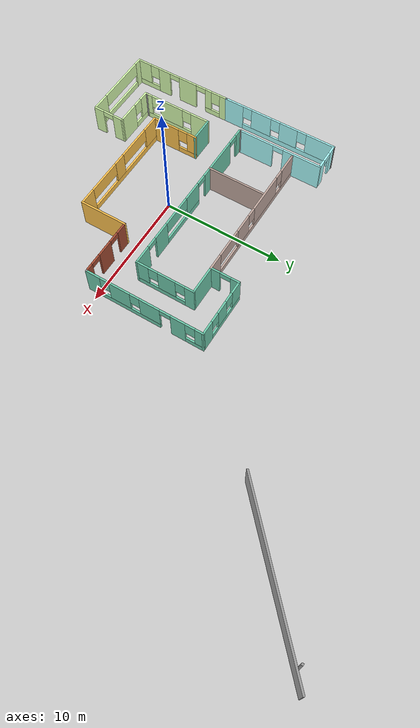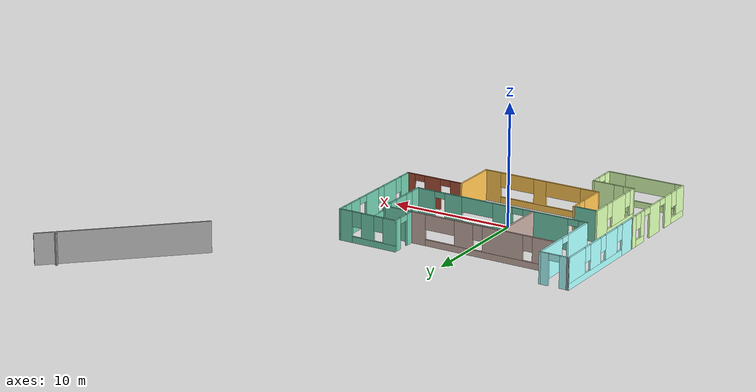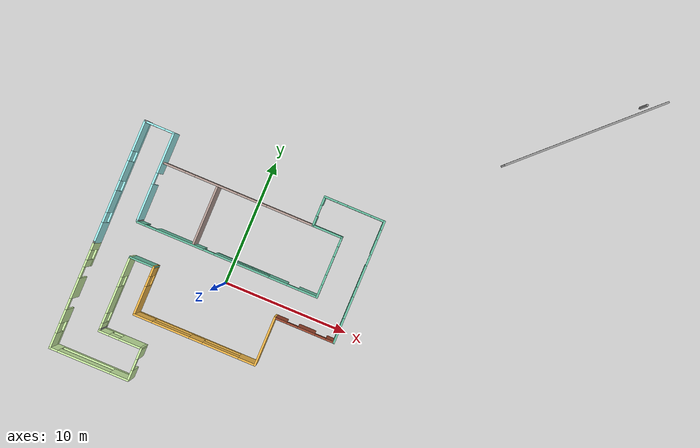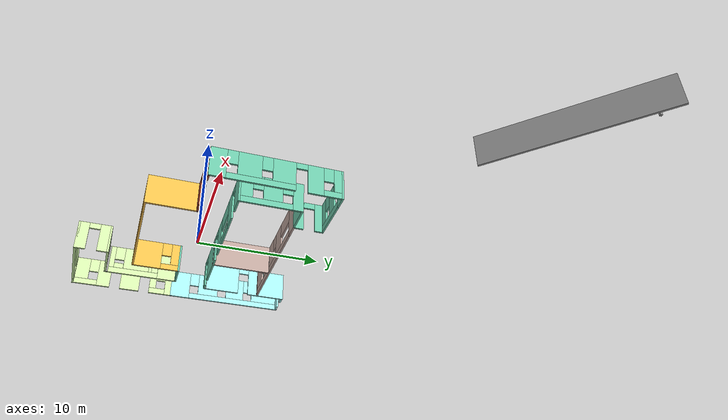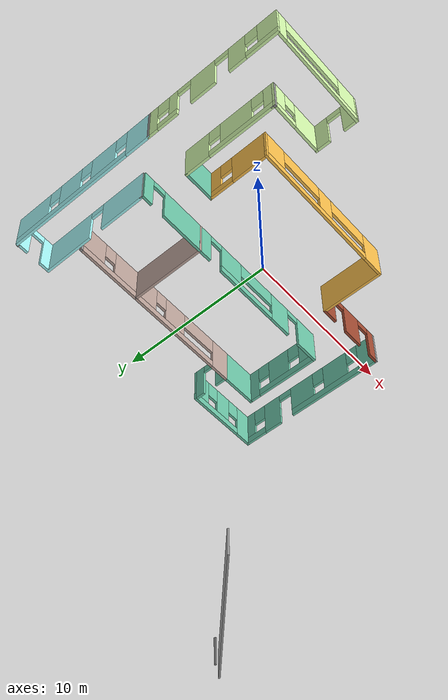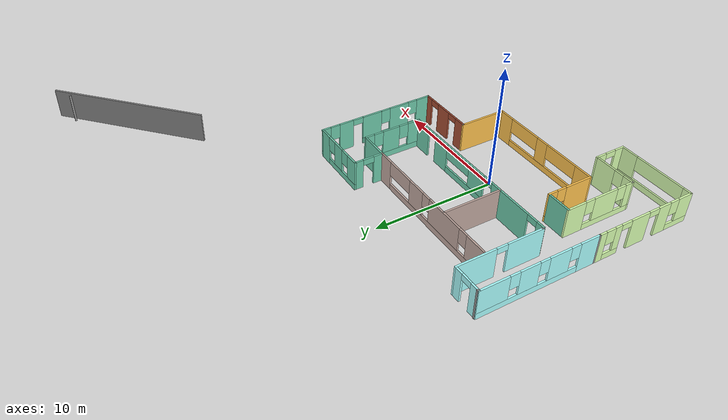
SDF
<?xml version='1.0'?>
<sdf version='1.6'>
  <model name='building'>
    <pose frame=''>7.75122 8.09541 0 0 -0 0</pose>
    <link name='Wall_0'>
      <pose frame=''>-8.08622 -12.7354 0 0 -0 3.14159</pose>
      <visual name='Wall_0_Visual_0'>
        <pose frame=''>-4.28694 0 1.25 0 -0 0</pose>
        <geometry>
          <box>
            <size>1.42611 0.15 2.5</size>
          </box>
        </geometry>
        <material>
          <script>
            <uri>file://media/materials/scripts/gazebo.material</uri>
            <name>Gazebo/Grey</name>
          </script>
          <ambient>1 0.764706 0.305882 1</ambient>
        </material>
        <meta>
          <layer>0</layer>
        </meta>
      </visual>
      <collision name='Wall_0_Collision_0'>
        <geometry>
          <box>
            <size>1.42611 0.15 2.5</size>
          </box>
        </geometry>
        <pose frame=''>-4.28694 0 1.25 0 -0 0</pose>
      </collision>
      <visual name='Wall_0_Visual_1'>
        <pose frame=''>0.713057 0 0.25 0 -0 0</pose>
        <geometry>
          <box>
            <size>8.57389 0.15 0.5</size>
          </box>
        </geometry>
        <material>
          <script>
            <uri>file://media/materials/scripts/gazebo.material</uri>
            <name>Gazebo/Grey</name>
          </script>
          <ambient>1 0.764706 0.305882 1</ambient>
        </material>
        <meta>
          <layer>0</layer>
        </meta>
      </visual>
      <collision name='Wall_0_Collision_1'>
        <geometry>
          <box>
            <size>8.57389 0.15 0.5</size>
          </box>
        </geometry>
        <pose frame=''>0.713057 0 0.25 0 -0 0</pose>
      </collision>
      <visual name='Wall_0_Visual_2'>
        <pose frame=''>-0.101719 0 1.5 0 -0 0</pose>
        <geometry>
          <box>
            <size>1.08588 0.15 2</size>
          </box>
        </geometry>
        <material>
          <script>
            <uri>file://media/materials/scripts/gazebo.material</uri>
            <name>Gazebo/Grey</name>
          </script>
          <ambient>1 0.764706 0.305882 1</ambient>
        </material>
        <meta>
          <layer>0</layer>
        </meta>
      </visual>
      <collision name='Wall_0_Collision_2'>
        <geometry>
          <box>
            <size>1.08588 0.15 2</size>
          </box>
        </geometry>
        <pose frame=''>-0.101719 0 1.5 0 -0 0</pose>
      </collision>
      <visual name='Wall_0_Visual_3'>
        <pose frame=''>4.22325 0 1.5 0 -0 0</pose>
        <geometry>
          <box>
            <size>1.55351 0.15 2</size>
          </box>
        </geometry>
        <material>
          <script>
            <uri>file://media/materials/scripts/gazebo.material</uri>
            <name>Gazebo/Grey</name>
          </script>
          <ambient>1 0.764706 0.305882 1</ambient>
        </material>
        <meta>
          <layer>0</layer>
        </meta>
      </visual>
      <collision name='Wall_0_Collision_3'>
        <geometry>
          <box>
            <size>1.55351 0.15 2</size>
          </box>
        </geometry>
        <pose frame=''>4.22325 0 1.5 0 -0 0</pose>
      </collision>
      <visual name='Wall_0_Visual_4'>
        <pose frame=''>-2.10927 0 1.9 0 -0 0</pose>
        <geometry>
          <box>
            <size>2.92923 0.15 1.2</size>
          </box>
        </geometry>
        <material>
          <script>
            <uri>file://media/materials/scripts/gazebo.material</uri>
            <name>Gazebo/Grey</name>
          </script>
          <ambient>1 0.764706 0.305882 1</ambient>
        </material>
        <meta>
          <layer>0</layer>
        </meta>
      </visual>
      <collision name='Wall_0_Collision_4'>
        <geometry>
          <box>
            <size>2.92923 0.15 1.2</size>
          </box>
        </geometry>
        <pose frame=''>-2.10927 0 1.9 0 -0 0</pose>
      </collision>
      <visual name='Wall_0_Visual_5'>
        <pose frame=''>1.94386 0 1.9 0 -0 0</pose>
        <geometry>
          <box>
            <size>3.00527 0.15 1.2</size>
          </box>
        </geometry>
        <material>
          <script>
            <uri>file://media/materials/scripts/gazebo.material</uri>
            <name>Gazebo/Grey</name>
          </script>
          <ambient>1 0.764706 0.305882 1</ambient>
        </material>
        <meta>
          <layer>0</layer>
        </meta>
      </visual>
      <collision name='Wall_0_Collision_5'>
        <geometry>
          <box>
            <size>3.00527 0.15 1.2</size>
          </box>
        </geometry>
        <pose frame=''>1.94386 0 1.9 0 -0 0</pose>
      </collision>
    </link>
    <link name='Wall_1'>
      <pose frame=''>-13.0112 -10.8104 0 0 -0 1.5708</pose>
      <visual name='Wall_1_Visual_0'>
        <pose frame=''>-0.814985 0 1.25 0 -0 0</pose>
        <geometry>
          <box>
            <size>2.37003 0.15 2.5</size>
          </box>
        </geometry>
        <material>
          <script>
            <uri>file://media/materials/scripts/gazebo.material</uri>
            <name>Gazebo/Grey</name>
          </script>
          <ambient>1 0.764706 0.305882 1</ambient>
        </material>
        <meta>
          <layer>0</layer>
        </meta>
      </visual>
      <collision name='Wall_1_Collision_0'>
        <geometry>
          <box>
            <size>2.37003 0.15 2.5</size>
          </box>
        </geometry>
        <pose frame=''>-0.814985 0 1.25 0 -0 0</pose>
      </collision>
      <visual name='Wall_1_Visual_1'>
        <pose frame=''>1.18501 0 0.25 0 -0 0</pose>
        <geometry>
          <box>
            <size>1.62997 0.15 0.5</size>
          </box>
        </geometry>
        <material>
          <script>
            <uri>file://media/materials/scripts/gazebo.material</uri>
            <name>Gazebo/Grey</name>
          </script>
          <ambient>1 0.764706 0.305882 1</ambient>
        </material>
        <meta>
          <layer>0</layer>
        </meta>
      </visual>
      <collision name='Wall_1_Collision_1'>
        <geometry>
          <box>
            <size>1.62997 0.15 0.5</size>
          </box>
        </geometry>
        <pose frame=''>1.18501 0 0.25 0 -0 0</pose>
      </collision>
      <visual name='Wall_1_Visual_2'>
        <pose frame=''>1.58502 0 1.5 0 -0 0</pose>
        <geometry>
          <box>
            <size>0.82997 0.15 2</size>
          </box>
        </geometry>
        <material>
          <script>
            <uri>file://media/materials/scripts/gazebo.material</uri>
            <name>Gazebo/Grey</name>
          </script>
          <ambient>1 0.764706 0.305882 1</ambient>
        </material>
        <meta>
          <layer>0</layer>
        </meta>
      </visual>
      <collision name='Wall_1_Collision_2'>
        <geometry>
          <box>
            <size>0.82997 0.15 2</size>
          </box>
        </geometry>
        <pose frame=''>1.58502 0 1.5 0 -0 0</pose>
      </collision>
      <visual name='Wall_1_Visual_3'>
        <pose frame=''>0.77003 0 1.9 0 -0 0</pose>
        <geometry>
          <box>
            <size>0.8 0.15 1.2</size>
          </box>
        </geometry>
        <material>
          <script>
            <uri>file://media/materials/scripts/gazebo.material</uri>
            <name>Gazebo/Grey</name>
          </script>
          <ambient>1 0.764706 0.305882 1</ambient>
        </material>
        <meta>
          <layer>0</layer>
        </meta>
      </visual>
      <collision name='Wall_1_Collision_3'>
        <geometry>
          <box>
            <size>0.8 0.15 1.2</size>
          </box>
        </geometry>
        <pose frame=''>0.77003 0 1.9 0 -0 0</pose>
      </collision>
    </link>
    <link name='Wall_10'>
      <collision name='Wall_10_Collision'>
        <geometry>
          <box>
            <size>0.15 0.15 2.5</size>
          </box>
        </geometry>
        <pose frame=''>0 0 1.25 0 -0 0</pose>
      </collision>
      <visual name='Wall_10_Visual'>
        <pose frame=''>0 0 1.25 0 -0 0</pose>
        <geometry>
          <box>
            <size>0.15 0.15 2.5</size>
          </box>
        </geometry>
        <material>
          <script>
            <uri>file://media/materials/scripts/gazebo.material</uri>
            <name>Gazebo/Grey</name>
          </script>
          <ambient>1 1 1 1</ambient>
        </material>
        <meta>
          <layer>0</layer>
        </meta>
      </visual>
      <pose frame=''>-17.8612 -8.88541 0 0 -0 0</pose>
    </link>
    <link name='Wall_11'>
      <collision name='Wall_11_Collision'>
        <geometry>
          <box>
            <size>0.15 0.15 2.5</size>
          </box>
        </geometry>
        <pose frame=''>0 0 1.25 0 -0 0</pose>
      </collision>
      <visual name='Wall_11_Visual'>
        <pose frame=''>0 0 1.25 0 -0 0</pose>
        <geometry>
          <box>
            <size>0.15 0.15 2.5</size>
          </box>
        </geometry>
        <material>
          <script>
            <uri>file://media/materials/scripts/gazebo.material</uri>
            <name>Gazebo/Grey</name>
          </script>
          <ambient>1 1 1 1</ambient>
        </material>
        <meta>
          <layer>0</layer>
        </meta>
      </visual>
      <pose frame=''>-17.8612 -8.88541 0 0 -0 0</pose>
    </link>
    <link name='Wall_13'>
      <collision name='Wall_13_Collision'>
        <geometry>
          <box>
            <size>0.15 0.15 2.5</size>
          </box>
        </geometry>
        <pose frame=''>0 0 1.25 0 -0 0</pose>
      </collision>
      <visual name='Wall_13_Visual'>
        <pose frame=''>0 0 1.25 0 -0 0</pose>
        <geometry>
          <box>
            <size>0.15 0.15 2.5</size>
          </box>
        </geometry>
        <material>
          <script>
            <uri>file://media/materials/scripts/gazebo.material</uri>
            <name>Gazebo/Grey</name>
          </script>
          <ambient>1 1 1 1</ambient>
        </material>
        <meta>
          <layer>0</layer>
        </meta>
      </visual>
      <pose frame=''>-17.8612 -8.88541 0 0 -0 0</pose>
    </link>
    <link name='Wall_16'>
      <collision name='Wall_16_Collision'>
        <geometry>
          <box>
            <size>0.15 0.15 2.5</size>
          </box>
        </geometry>
        <pose frame=''>0 0 1.25 0 -0 0</pose>
      </collision>
      <visual name='Wall_16_Visual'>
        <pose frame=''>0 0 1.25 0 -0 0</pose>
        <geometry>
          <box>
            <size>0.15 0.15 2.5</size>
          </box>
        </geometry>
        <material>
          <script>
            <uri>file://media/materials/scripts/gazebo.material</uri>
            <name>Gazebo/Grey</name>
          </script>
          <ambient>1 1 1 1</ambient>
        </material>
        <meta>
          <layer>0</layer>
        </meta>
      </visual>
      <pose frame=''>-17.7916 1.00147 0 0 -0 0</pose>
    </link>
    <link name='Wall_19'>
      <collision name='Wall_19_Collision'>
        <geometry>
          <box>
            <size>13.2246 0.15 2.5</size>
          </box>
        </geometry>
        <pose frame=''>0 0 1.25 0 -0 0</pose>
      </collision>
      <visual name='Wall_19_Visual'>
        <pose frame=''>0 0 1.25 0 -0 0</pose>
        <geometry>
          <box>
            <size>13.2246 0.15 2.5</size>
          </box>
        </geometry>
        <material>
          <script>
            <uri>file://media/materials/scripts/gazebo.material</uri>
            <name>Gazebo/Grey</name>
          </script>
          <ambient>1 1 1 1</ambient>
        </material>
        <meta>
          <layer>0</layer>
        </meta>
      </visual>
      <pose frame=''>13.1096 12.9319 0 0 0 -2.37763</pose>
    </link>
    <link name='Wall_20'>
      <collision name='Wall_20_Collision'>
        <geometry>
          <box>
            <size>0.15 0.15 2.5</size>
          </box>
        </geometry>
        <pose frame=''>0 0 1.25 0 -0 0</pose>
      </collision>
      <visual name='Wall_20_Visual'>
        <pose frame=''>0 0 1.25 0 -0 0</pose>
        <geometry>
          <box>
            <size>0.15 0.15 2.5</size>
          </box>
        </geometry>
        <material>
          <script>
            <uri>file://media/materials/scripts/gazebo.material</uri>
            <name>Gazebo/Grey</name>
          </script>
          <ambient>1 1 1 1</ambient>
        </material>
        <meta>
          <layer>0</layer>
        </meta>
      </visual>
      <pose frame=''>16.475 16.6544 0 0 -0 0</pose>
    </link>
    <link name='Wall_22'>
      <pose frame=''>1.65837 -3.96041 0 0 -0 1.5708</pose>
      <visual name='Wall_22_Visual_0'>
        <pose frame=''>-4.3788 0 1.25 0 -0 0</pose>
        <geometry>
          <box>
            <size>1.2424 0.15 2.5</size>
          </box>
        </geometry>
        <material>
          <script>
            <uri>file://media/materials/scripts/gazebo.material</uri>
            <name>Gazebo/Grey</name>
          </script>
          <ambient>0.435294 0.796078 0.67451 1</ambient>
        </material>
        <meta>
          <layer>0</layer>
        </meta>
      </visual>
      <collision name='Wall_22_Collision_0'>
        <geometry>
          <box>
            <size>1.2424 0.15 2.5</size>
          </box>
        </geometry>
        <pose frame=''>-4.3788 0 1.25 0 -0 0</pose>
      </collision>
      <visual name='Wall_22_Visual_1'>
        <pose frame=''>2.84528 0 1.25 0 -0 0</pose>
        <geometry>
          <box>
            <size>1.21212 0.15 2.5</size>
          </box>
        </geometry>
        <material>
          <script>
            <uri>file://media/materials/scripts/gazebo.material</uri>
            <name>Gazebo/Grey</name>
          </script>
          <ambient>0.435294 0.796078 0.67451 1</ambient>
        </material>
        <meta>
          <layer>0</layer>
        </meta>
      </visual>
      <collision name='Wall_22_Collision_1'>
        <geometry>
          <box>
            <size>1.21212 0.15 2.5</size>
          </box>
        </geometry>
        <pose frame=''>2.84528 0 1.25 0 -0 0</pose>
      </collision>
      <visual name='Wall_22_Visual_2'>
        <pose frame=''>-1.20919 0 0.25 0 -0 0</pose>
        <geometry>
          <box>
            <size>5.09682 0.15 0.5</size>
          </box>
        </geometry>
        <material>
          <script>
            <uri>file://media/materials/scripts/gazebo.material</uri>
            <name>Gazebo/Grey</name>
          </script>
          <ambient>0.435294 0.796078 0.67451 1</ambient>
        </material>
        <meta>
          <layer>0</layer>
        </meta>
      </visual>
      <collision name='Wall_22_Collision_2'>
        <geometry>
          <box>
            <size>5.09682 0.15 0.5</size>
          </box>
        </geometry>
        <pose frame=''>-1.20919 0 0.25 0 -0 0</pose>
      </collision>
      <visual name='Wall_22_Visual_3'>
        <pose frame=''>4.22567 0 0.25 0 -0 0</pose>
        <geometry>
          <box>
            <size>1.54866 0.15 0.5</size>
          </box>
        </geometry>
        <material>
          <script>
            <uri>file://media/materials/scripts/gazebo.material</uri>
            <name>Gazebo/Grey</name>
          </script>
          <ambient>0.435294 0.796078 0.67451 1</ambient>
        </material>
        <meta>
          <layer>0</layer>
        </meta>
      </visual>
      <collision name='Wall_22_Collision_3'>
        <geometry>
          <box>
            <size>1.54866 0.15 0.5</size>
          </box>
        </geometry>
        <pose frame=''>4.22567 0 0.25 0 -0 0</pose>
      </collision>
      <visual name='Wall_22_Visual_4'>
        <pose frame=''>-2.07246 0 1.5 0 -0 0</pose>
        <geometry>
          <box>
            <size>1.77028 0.15 2</size>
          </box>
        </geometry>
        <material>
          <script>
            <uri>file://media/materials/scripts/gazebo.material</uri>
            <name>Gazebo/Grey</name>
          </script>
          <ambient>0.435294 0.796078 0.67451 1</ambient>
        </material>
        <meta>
          <layer>0</layer>
        </meta>
      </visual>
      <collision name='Wall_22_Collision_4'>
        <geometry>
          <box>
            <size>1.77028 0.15 2</size>
          </box>
        </geometry>
        <pose frame=''>-2.07246 0 1.5 0 -0 0</pose>
      </collision>
      <visual name='Wall_22_Visual_5'>
        <pose frame=''>0.475947 0 1.5 0 -0 0</pose>
        <geometry>
          <box>
            <size>1.72654 0.15 2</size>
          </box>
        </geometry>
        <material>
          <script>
            <uri>file://media/materials/scripts/gazebo.material</uri>
            <name>Gazebo/Grey</name>
          </script>
          <ambient>0.435294 0.796078 0.67451 1</ambient>
        </material>
        <meta>
          <layer>0</layer>
        </meta>
      </visual>
      <collision name='Wall_22_Collision_5'>
        <geometry>
          <box>
            <size>1.72654 0.15 2</size>
          </box>
        </geometry>
        <pose frame=''>0.475947 0 1.5 0 -0 0</pose>
      </collision>
      <visual name='Wall_22_Visual_6'>
        <pose frame=''>0.475947 0 1.5 0 -0 0</pose>
        <geometry>
          <box>
            <size>1.72654 0.15 2</size>
          </box>
        </geometry>
        <material>
          <script>
            <uri>file://media/materials/scripts/gazebo.material</uri>
            <name>Gazebo/Grey</name>
          </script>
          <ambient>0.435294 0.796078 0.67451 1</ambient>
        </material>
        <meta>
          <layer>0</layer>
        </meta>
      </visual>
      <collision name='Wall_22_Collision_6'>
        <geometry>
          <box>
            <size>1.72654 0.15 2</size>
          </box>
        </geometry>
        <pose frame=''>0.475947 0 1.5 0 -0 0</pose>
      </collision>
      <visual name='Wall_22_Visual_7'>
        <pose frame=''>4.62567 0 1.5 0 -0 0</pose>
        <geometry>
          <box>
            <size>0.748656 0.15 2</size>
          </box>
        </geometry>
        <material>
          <script>
            <uri>file://media/materials/scripts/gazebo.material</uri>
            <name>Gazebo/Grey</name>
          </script>
          <ambient>0.435294 0.796078 0.67451 1</ambient>
        </material>
        <meta>
          <layer>0</layer>
        </meta>
      </visual>
      <collision name='Wall_22_Collision_7'>
        <geometry>
          <box>
            <size>0.748656 0.15 2</size>
          </box>
        </geometry>
        <pose frame=''>4.62567 0 1.5 0 -0 0</pose>
      </collision>
      <visual name='Wall_22_Visual_8'>
        <pose frame=''>-3.3576 0 1.9 0 -0 0</pose>
        <geometry>
          <box>
            <size>0.8 0.15 1.2</size>
          </box>
        </geometry>
        <material>
          <script>
            <uri>file://media/materials/scripts/gazebo.material</uri>
            <name>Gazebo/Grey</name>
          </script>
          <ambient>0.435294 0.796078 0.67451 1</ambient>
        </material>
        <meta>
          <layer>0</layer>
        </meta>
      </visual>
      <collision name='Wall_22_Collision_8'>
        <geometry>
          <box>
            <size>0.8 0.15 1.2</size>
          </box>
        </geometry>
        <pose frame=''>-3.3576 0 1.9 0 -0 0</pose>
      </collision>
      <visual name='Wall_22_Visual_9'>
        <pose frame=''>3.85134 0 1.9 0 -0 0</pose>
        <geometry>
          <box>
            <size>0.8 0.15 1.2</size>
          </box>
        </geometry>
        <material>
          <script>
            <uri>file://media/materials/scripts/gazebo.material</uri>
            <name>Gazebo/Grey</name>
          </script>
          <ambient>0.435294 0.796078 0.67451 1</ambient>
        </material>
        <meta>
          <layer>0</layer>
        </meta>
      </visual>
      <collision name='Wall_22_Collision_9'>
        <geometry>
          <box>
            <size>0.8 0.15 1.2</size>
          </box>
        </geometry>
        <pose frame=''>3.85134 0 1.9 0 -0 0</pose>
      </collision>
      <visual name='Wall_22_Visual_10'>
        <pose frame=''>-0.787325 0 1.9 0 -0 0</pose>
        <geometry>
          <box>
            <size>0.8 0.15 1.2</size>
          </box>
        </geometry>
        <material>
          <script>
            <uri>file://media/materials/scripts/gazebo.material</uri>
            <name>Gazebo/Grey</name>
          </script>
          <ambient>0.435294 0.796078 0.67451 1</ambient>
        </material>
        <meta>
          <layer>0</layer>
        </meta>
      </visual>
      <collision name='Wall_22_Collision_10'>
        <geometry>
          <box>
            <size>0.8 0.15 1.2</size>
          </box>
        </geometry>
        <pose frame=''>-0.787325 0 1.9 0 -0 0</pose>
      </collision>
      <visual name='Wall_22_Visual_11'>
        <pose frame=''>1.78922 0 2.25 0 -0 0</pose>
        <geometry>
          <box>
            <size>0.9 0.15 0.5</size>
          </box>
        </geometry>
        <material>
          <script>
            <uri>file://media/materials/scripts/gazebo.material</uri>
            <name>Gazebo/Grey</name>
          </script>
          <ambient>0.435294 0.796078 0.67451 1</ambient>
        </material>
        <meta>
          <layer>0</layer>
        </meta>
      </visual>
      <collision name='Wall_22_Collision_11'>
        <geometry>
          <box>
            <size>0.9 0.15 0.5</size>
          </box>
        </geometry>
        <pose frame=''>1.78922 0 2.25 0 -0 0</pose>
      </collision>
      <visual name='Wall_22_Visual_12'>
        <pose frame=''>1.78922 0 2.25 0 -0 0</pose>
        <geometry>
          <box>
            <size>0.9 0.15 0.5</size>
          </box>
        </geometry>
        <material>
          <script>
            <uri>file://media/materials/scripts/gazebo.material</uri>
            <name>Gazebo/Grey</name>
          </script>
          <ambient>0.435294 0.796078 0.67451 1</ambient>
        </material>
        <meta>
          <layer>0</layer>
        </meta>
      </visual>
      <collision name='Wall_22_Collision_12'>
        <geometry>
          <box>
            <size>0.9 0.15 0.5</size>
          </box>
        </geometry>
        <pose frame=''>1.78922 0 2.25 0 -0 0</pose>
      </collision>
    </link>
    <link name='Wall_23'>
      <pose frame=''>-0.766634 0.964587 0 0 -0 3.14159</pose>
      <visual name='Wall_23_Visual_0'>
        <pose frame=''>-1.90941 0 1.25 0 -0 0</pose>
        <geometry>
          <box>
            <size>1.18118 0.15 2.5</size>
          </box>
        </geometry>
        <material>
          <script>
            <uri>file://media/materials/scripts/gazebo.material</uri>
            <name>Gazebo/Grey</name>
          </script>
          <ambient>0.435294 0.796078 0.67451 1</ambient>
        </material>
        <meta>
          <layer>0</layer>
        </meta>
      </visual>
      <collision name='Wall_23_Collision_0'>
        <geometry>
          <box>
            <size>1.18118 0.15 2.5</size>
          </box>
        </geometry>
        <pose frame=''>-1.90941 0 1.25 0 -0 0</pose>
      </collision>
      <visual name='Wall_23_Visual_1'>
        <pose frame=''>0.590591 0 0.25 0 -0 0</pose>
        <geometry>
          <box>
            <size>3.81882 0.15 0.5</size>
          </box>
        </geometry>
        <material>
          <script>
            <uri>file://media/materials/scripts/gazebo.material</uri>
            <name>Gazebo/Grey</name>
          </script>
          <ambient>0.435294 0.796078 0.67451 1</ambient>
        </material>
        <meta>
          <layer>0</layer>
        </meta>
      </visual>
      <collision name='Wall_23_Collision_1'>
        <geometry>
          <box>
            <size>3.81882 0.15 0.5</size>
          </box>
        </geometry>
        <pose frame=''>0.590591 0 0.25 0 -0 0</pose>
      </collision>
      <visual name='Wall_23_Visual_2'>
        <pose frame=''>0.031729 0 1.5 0 -0 0</pose>
        <geometry>
          <box>
            <size>1.10109 0.15 2</size>
          </box>
        </geometry>
        <material>
          <script>
            <uri>file://media/materials/scripts/gazebo.material</uri>
            <name>Gazebo/Grey</name>
          </script>
          <ambient>0.435294 0.796078 0.67451 1</ambient>
        </material>
        <meta>
          <layer>0</layer>
        </meta>
      </visual>
      <collision name='Wall_23_Collision_2'>
        <geometry>
          <box>
            <size>1.10109 0.15 2</size>
          </box>
        </geometry>
        <pose frame=''>0.031729 0 1.5 0 -0 0</pose>
      </collision>
      <visual name='Wall_23_Visual_3'>
        <pose frame=''>1.94114 0 1.5 0 -0 0</pose>
        <geometry>
          <box>
            <size>1.11772 0.15 2</size>
          </box>
        </geometry>
        <material>
          <script>
            <uri>file://media/materials/scripts/gazebo.material</uri>
            <name>Gazebo/Grey</name>
          </script>
          <ambient>0.435294 0.796078 0.67451 1</ambient>
        </material>
        <meta>
          <layer>0</layer>
        </meta>
      </visual>
      <collision name='Wall_23_Collision_3'>
        <geometry>
          <box>
            <size>1.11772 0.15 2</size>
          </box>
        </geometry>
        <pose frame=''>1.94114 0 1.5 0 -0 0</pose>
      </collision>
      <visual name='Wall_23_Visual_4'>
        <pose frame=''>-0.918818 0 1.9 0 -0 0</pose>
        <geometry>
          <box>
            <size>0.8 0.15 1.2</size>
          </box>
        </geometry>
        <material>
          <script>
            <uri>file://media/materials/scripts/gazebo.material</uri>
            <name>Gazebo/Grey</name>
          </script>
          <ambient>0.435294 0.796078 0.67451 1</ambient>
        </material>
        <meta>
          <layer>0</layer>
        </meta>
      </visual>
      <collision name='Wall_23_Collision_4'>
        <geometry>
          <box>
            <size>0.8 0.15 1.2</size>
          </box>
        </geometry>
        <pose frame=''>-0.918818 0 1.9 0 -0 0</pose>
      </collision>
      <visual name='Wall_23_Visual_5'>
        <pose frame=''>0.982276 0 1.9 0 -0 0</pose>
        <geometry>
          <box>
            <size>0.8 0.15 1.2</size>
          </box>
        </geometry>
        <material>
          <script>
            <uri>file://media/materials/scripts/gazebo.material</uri>
            <name>Gazebo/Grey</name>
          </script>
          <ambient>0.435294 0.796078 0.67451 1</ambient>
        </material>
        <meta>
          <layer>0</layer>
        </meta>
      </visual>
      <collision name='Wall_23_Collision_5'>
        <geometry>
          <box>
            <size>0.8 0.15 1.2</size>
          </box>
        </geometry>
        <pose frame=''>0.982276 0 1.9 0 -0 0</pose>
      </collision>
    </link>
    <link name='Wall_24'>
      <pose frame=''>-3.19163 -0.210413 0 0 0 -1.5708</pose>
      <visual name='Wall_24_Visual_0'>
        <pose frame=''>-0.870254 0 1.25 0 -0 0</pose>
        <geometry>
          <box>
            <size>0.759491 0.15 2.5</size>
          </box>
        </geometry>
        <material>
          <script>
            <uri>file://media/materials/scripts/gazebo.material</uri>
            <name>Gazebo/Grey</name>
          </script>
          <ambient>0.435294 0.796078 0.67451 1</ambient>
        </material>
        <meta>
          <layer>0</layer>
        </meta>
      </visual>
      <collision name='Wall_24_Collision_0'>
        <geometry>
          <box>
            <size>0.759491 0.15 2.5</size>
          </box>
        </geometry>
        <pose frame=''>-0.870254 0 1.25 0 -0 0</pose>
      </collision>
      <visual name='Wall_24_Visual_1'>
        <pose frame=''>0.829746 0 1.25 0 -0 0</pose>
        <geometry>
          <box>
            <size>0.840509 0.15 2.5</size>
          </box>
        </geometry>
        <material>
          <script>
            <uri>file://media/materials/scripts/gazebo.material</uri>
            <name>Gazebo/Grey</name>
          </script>
          <ambient>0.435294 0.796078 0.67451 1</ambient>
        </material>
        <meta>
          <layer>0</layer>
        </meta>
      </visual>
      <collision name='Wall_24_Collision_1'>
        <geometry>
          <box>
            <size>0.840509 0.15 2.5</size>
          </box>
        </geometry>
        <pose frame=''>0.829746 0 1.25 0 -0 0</pose>
      </collision>
      <visual name='Wall_24_Visual_2'>
        <pose frame=''>-0.040509 0 2.25 0 -0 0</pose>
        <geometry>
          <box>
            <size>0.9 0.15 0.5</size>
          </box>
        </geometry>
        <material>
          <script>
            <uri>file://media/materials/scripts/gazebo.material</uri>
            <name>Gazebo/Grey</name>
          </script>
          <ambient>0.435294 0.796078 0.67451 1</ambient>
        </material>
        <meta>
          <layer>0</layer>
        </meta>
      </visual>
      <collision name='Wall_24_Collision_2'>
        <geometry>
          <box>
            <size>0.9 0.15 0.5</size>
          </box>
        </geometry>
        <pose frame=''>-0.040509 0 2.25 0 -0 0</pose>
      </collision>
    </link>
    <link name='Wall_25'>
      <collision name='Wall_25_Collision'>
        <geometry>
          <box>
            <size>2.5 0.15 2.5</size>
          </box>
        </geometry>
        <pose frame=''>0 0 1.25 0 -0 0</pose>
      </collision>
      <visual name='Wall_25_Visual'>
        <pose frame=''>0 0 1.25 0 -0 0</pose>
        <geometry>
          <box>
            <size>2.5 0.15 2.5</size>
          </box>
        </geometry>
        <material>
          <script>
            <uri>file://media/materials/scripts/gazebo.material</uri>
            <name>Gazebo/Grey</name>
          </script>
          <ambient>0.435294 0.796078 0.67451 1</ambient>
        </material>
        <meta>
          <layer>0</layer>
        </meta>
      </visual>
      <pose frame=''>-2.01663 -1.38541 0 0 -0 0</pose>
    </link>
    <link name='Wall_26'>
      <pose frame=''>-0.841634 -3.81041 0 0 0 -1.5708</pose>
      <visual name='Wall_26_Visual_0'>
        <pose frame=''>-2.09158 0 1.25 0 -0 0</pose>
        <geometry>
          <box>
            <size>0.816847 0.15 2.5</size>
          </box>
        </geometry>
        <material>
          <script>
            <uri>file://media/materials/scripts/gazebo.material</uri>
            <name>Gazebo/Grey</name>
          </script>
          <ambient>0.435294 0.796078 0.67451 1</ambient>
        </material>
        <meta>
          <layer>0</layer>
        </meta>
      </visual>
      <collision name='Wall_26_Collision_0'>
        <geometry>
          <box>
            <size>0.816847 0.15 2.5</size>
          </box>
        </geometry>
        <pose frame=''>-2.09158 0 1.25 0 -0 0</pose>
      </collision>
      <visual name='Wall_26_Visual_1'>
        <pose frame=''>0.408424 0 0.25 0 -0 0</pose>
        <geometry>
          <box>
            <size>4.18315 0.15 0.5</size>
          </box>
        </geometry>
        <material>
          <script>
            <uri>file://media/materials/scripts/gazebo.material</uri>
            <name>Gazebo/Grey</name>
          </script>
          <ambient>0.435294 0.796078 0.67451 1</ambient>
        </material>
        <meta>
          <layer>0</layer>
        </meta>
      </visual>
      <collision name='Wall_26_Collision_1'>
        <geometry>
          <box>
            <size>4.18315 0.15 0.5</size>
          </box>
        </geometry>
        <pose frame=''>0.408424 0 0.25 0 -0 0</pose>
      </collision>
      <visual name='Wall_26_Visual_2'>
        <pose frame=''>-0.134892 0 1.5 0 -0 0</pose>
        <geometry>
          <box>
            <size>1.49652 0.15 2</size>
          </box>
        </geometry>
        <material>
          <script>
            <uri>file://media/materials/scripts/gazebo.material</uri>
            <name>Gazebo/Grey</name>
          </script>
          <ambient>0.435294 0.796078 0.67451 1</ambient>
        </material>
        <meta>
          <layer>0</layer>
        </meta>
      </visual>
      <collision name='Wall_26_Collision_2'>
        <geometry>
          <box>
            <size>1.49652 0.15 2</size>
          </box>
        </geometry>
        <pose frame=''>-0.134892 0 1.5 0 -0 0</pose>
      </collision>
      <visual name='Wall_26_Visual_3'>
        <pose frame=''>1.95668 0 1.5 0 -0 0</pose>
        <geometry>
          <box>
            <size>1.08663 0.15 2</size>
          </box>
        </geometry>
        <material>
          <script>
            <uri>file://media/materials/scripts/gazebo.material</uri>
            <name>Gazebo/Grey</name>
          </script>
          <ambient>0.435294 0.796078 0.67451 1</ambient>
        </material>
        <meta>
          <layer>0</layer>
        </meta>
      </visual>
      <collision name='Wall_26_Collision_3'>
        <geometry>
          <box>
            <size>1.08663 0.15 2</size>
          </box>
        </geometry>
        <pose frame=''>1.95668 0 1.5 0 -0 0</pose>
      </collision>
      <visual name='Wall_26_Visual_4'>
        <pose frame=''>-1.28315 0 1.9 0 -0 0</pose>
        <geometry>
          <box>
            <size>0.8 0.15 1.2</size>
          </box>
        </geometry>
        <material>
          <script>
            <uri>file://media/materials/scripts/gazebo.material</uri>
            <name>Gazebo/Grey</name>
          </script>
          <ambient>0.435294 0.796078 0.67451 1</ambient>
        </material>
        <meta>
          <layer>0</layer>
        </meta>
      </visual>
      <collision name='Wall_26_Collision_4'>
        <geometry>
          <box>
            <size>0.8 0.15 1.2</size>
          </box>
        </geometry>
        <pose frame=''>-1.28315 0 1.9 0 -0 0</pose>
      </collision>
      <visual name='Wall_26_Visual_5'>
        <pose frame=''>1.01337 0 1.9 0 -0 0</pose>
        <geometry>
          <box>
            <size>0.8 0.15 1.2</size>
          </box>
        </geometry>
        <material>
          <script>
            <uri>file://media/materials/scripts/gazebo.material</uri>
            <name>Gazebo/Grey</name>
          </script>
          <ambient>0.435294 0.796078 0.67451 1</ambient>
        </material>
        <meta>
          <layer>0</layer>
        </meta>
      </visual>
      <collision name='Wall_26_Collision_5'>
        <geometry>
          <box>
            <size>0.8 0.15 1.2</size>
          </box>
        </geometry>
        <pose frame=''>1.01337 0 1.9 0 -0 0</pose>
      </collision>
    </link>
    <link name='Wall_27'>
      <pose frame=''>-8.14163 -6.23541 0 0 -0 3.14159</pose>
      <visual name='Wall_27_Visual_0'>
        <pose frame=''>-6.57656 0 1.25 0 -0 0</pose>
        <geometry>
          <box>
            <size>1.59689 0.15 2.5</size>
          </box>
        </geometry>
        <material>
          <script>
            <uri>file://media/materials/scripts/gazebo.material</uri>
            <name>Gazebo/Grey</name>
          </script>
          <ambient>0.435294 0.796078 0.67451 1</ambient>
        </material>
        <meta>
          <layer>0</layer>
        </meta>
      </visual>
      <collision name='Wall_27_Collision_0'>
        <geometry>
          <box>
            <size>1.59689 0.15 2.5</size>
          </box>
        </geometry>
        <pose frame=''>-6.57656 0 1.25 0 -0 0</pose>
      </collision>
      <visual name='Wall_27_Visual_1'>
        <pose frame=''>-4.12443 0 1.25 0 -0 0</pose>
        <geometry>
          <box>
            <size>1.50736 0.15 2.5</size>
          </box>
        </geometry>
        <material>
          <script>
            <uri>file://media/materials/scripts/gazebo.material</uri>
            <name>Gazebo/Grey</name>
          </script>
          <ambient>0.435294 0.796078 0.67451 1</ambient>
        </material>
        <meta>
          <layer>0</layer>
        </meta>
      </visual>
      <collision name='Wall_27_Collision_1'>
        <geometry>
          <box>
            <size>1.50736 0.15 2.5</size>
          </box>
        </geometry>
        <pose frame=''>-4.12443 0 1.25 0 -0 0</pose>
      </collision>
      <visual name='Wall_27_Visual_2'>
        <pose frame=''>3.86558 0 1.25 0 -0 0</pose>
        <geometry>
          <box>
            <size>3.82992 0.15 2.5</size>
          </box>
        </geometry>
        <material>
          <script>
            <uri>file://media/materials/scripts/gazebo.material</uri>
            <name>Gazebo/Grey</name>
          </script>
          <ambient>0.435294 0.796078 0.67451 1</ambient>
        </material>
        <meta>
          <layer>0</layer>
        </meta>
      </visual>
      <collision name='Wall_27_Collision_2'>
        <geometry>
          <box>
            <size>3.82992 0.15 2.5</size>
          </box>
        </geometry>
        <pose frame=''>3.86558 0 1.25 0 -0 0</pose>
      </collision>
      <visual name='Wall_27_Visual_3'>
        <pose frame=''>7.02777 0 1.25 0 -0 0</pose>
        <geometry>
          <box>
            <size>0.694461 0.15 2.5</size>
          </box>
        </geometry>
        <material>
          <script>
            <uri>file://media/materials/scripts/gazebo.material</uri>
            <name>Gazebo/Grey</name>
          </script>
          <ambient>0.435294 0.796078 0.67451 1</ambient>
        </material>
        <meta>
          <layer>0</layer>
        </meta>
      </visual>
      <collision name='Wall_27_Collision_3'>
        <geometry>
          <box>
            <size>0.694461 0.15 2.5</size>
          </box>
        </geometry>
        <pose frame=''>7.02777 0 1.25 0 -0 0</pose>
      </collision>
      <visual name='Wall_27_Visual_4'>
        <pose frame=''>-1.16007 0 0.25 0 -0 0</pose>
        <geometry>
          <box>
            <size>4.42137 0.15 0.5</size>
          </box>
        </geometry>
        <material>
          <script>
            <uri>file://media/materials/scripts/gazebo.material</uri>
            <name>Gazebo/Grey</name>
          </script>
          <ambient>0.435294 0.796078 0.67451 1</ambient>
        </material>
        <meta>
          <layer>0</layer>
        </meta>
      </visual>
      <collision name='Wall_27_Collision_4'>
        <geometry>
          <box>
            <size>4.42137 0.15 0.5</size>
          </box>
        </geometry>
        <pose frame=''>-1.16007 0 0.25 0 -0 0</pose>
      </collision>
      <visual name='Wall_27_Visual_5'>
        <pose frame=''>0.198082 0 1.5 0 -0 0</pose>
        <geometry>
          <box>
            <size>1.70507 0.15 2</size>
          </box>
        </geometry>
        <material>
          <script>
            <uri>file://media/materials/scripts/gazebo.material</uri>
            <name>Gazebo/Grey</name>
          </script>
          <ambient>0.435294 0.796078 0.67451 1</ambient>
        </material>
        <meta>
          <layer>0</layer>
        </meta>
      </visual>
      <collision name='Wall_27_Collision_5'>
        <geometry>
          <box>
            <size>1.70507 0.15 2</size>
          </box>
        </geometry>
        <pose frame=''>0.198082 0 1.5 0 -0 0</pose>
      </collision>
      <visual name='Wall_27_Visual_6'>
        <pose frame=''>-2.0126 0 1.9 0 -0 0</pose>
        <geometry>
          <box>
            <size>2.7163 0.15 1.2</size>
          </box>
        </geometry>
        <material>
          <script>
            <uri>file://media/materials/scripts/gazebo.material</uri>
            <name>Gazebo/Grey</name>
          </script>
          <ambient>0.435294 0.796078 0.67451 1</ambient>
        </material>
        <meta>
          <layer>0</layer>
        </meta>
      </visual>
      <collision name='Wall_27_Collision_6'>
        <geometry>
          <box>
            <size>2.7163 0.15 1.2</size>
          </box>
        </geometry>
        <pose frame=''>-2.0126 0 1.9 0 -0 0</pose>
      </collision>
      <visual name='Wall_27_Visual_7'>
        <pose frame=''>-5.32811 0 2.25 0 -0 0</pose>
        <geometry>
          <box>
            <size>0.9 0.15 0.5</size>
          </box>
        </geometry>
        <material>
          <script>
            <uri>file://media/materials/scripts/gazebo.material</uri>
            <name>Gazebo/Grey</name>
          </script>
          <ambient>0.435294 0.796078 0.67451 1</ambient>
        </material>
        <meta>
          <layer>0</layer>
        </meta>
      </visual>
      <collision name='Wall_27_Collision_7'>
        <geometry>
          <box>
            <size>0.9 0.15 0.5</size>
          </box>
        </geometry>
        <pose frame=''>-5.32811 0 2.25 0 -0 0</pose>
      </collision>
      <visual name='Wall_27_Visual_8'>
        <pose frame=''>6.23054 0 2.25 0 -0 0</pose>
        <geometry>
          <box>
            <size>0.9 0.15 0.5</size>
          </box>
        </geometry>
        <material>
          <script>
            <uri>file://media/materials/scripts/gazebo.material</uri>
            <name>Gazebo/Grey</name>
          </script>
          <ambient>0.435294 0.796078 0.67451 1</ambient>
        </material>
        <meta>
          <layer>0</layer>
        </meta>
      </visual>
      <collision name='Wall_27_Collision_8'>
        <geometry>
          <box>
            <size>0.9 0.15 0.5</size>
          </box>
        </geometry>
        <pose frame=''>6.23054 0 2.25 0 -0 0</pose>
      </collision>
      <visual name='Wall_27_Visual_9'>
        <pose frame=''>1.50062 0 2.25 0 -0 0</pose>
        <geometry>
          <box>
            <size>0.9 0.15 0.5</size>
          </box>
        </geometry>
        <material>
          <script>
            <uri>file://media/materials/scripts/gazebo.material</uri>
            <name>Gazebo/Grey</name>
          </script>
          <ambient>0.435294 0.796078 0.67451 1</ambient>
        </material>
        <meta>
          <layer>0</layer>
        </meta>
      </visual>
      <collision name='Wall_27_Collision_9'>
        <geometry>
          <box>
            <size>0.9 0.15 0.5</size>
          </box>
        </geometry>
        <pose frame=''>1.50062 0 2.25 0 -0 0</pose>
      </collision>
    </link>
    <link name='Wall_3'>
      <collision name='Wall_3_Collision'>
        <geometry>
          <box>
            <size>4 0.15 2.5</size>
          </box>
        </geometry>
        <pose frame=''>0 0 1.25 0 -0 0</pose>
      </collision>
      <visual name='Wall_3_Visual'>
        <pose frame=''>0 0 1.25 0 -0 0</pose>
        <geometry>
          <box>
            <size>4 0.15 2.5</size>
          </box>
        </geometry>
        <material>
          <script>
            <uri>file://media/materials/scripts/gazebo.material</uri>
            <name>Gazebo/Grey</name>
          </script>
          <ambient>1 0.764706 0.305882 1</ambient>
        </material>
        <meta>
          <layer>0</layer>
        </meta>
      </visual>
      <pose frame=''>-3.16122 -10.8104 0 0 -0 1.5708</pose>
    </link>
    <link name='Wall_30'>
      <collision name='Wall_30_Collision'>
        <geometry>
          <box>
            <size>0.15 0.15 2.5</size>
          </box>
        </geometry>
        <pose frame=''>0 0 1.25 0 -0 0</pose>
      </collision>
      <visual name='Wall_30_Visual'>
        <pose frame=''>0 0 1.25 0 -0 0</pose>
        <geometry>
          <box>
            <size>0.15 0.15 2.5</size>
          </box>
        </geometry>
        <material>
          <script>
            <uri>file://media/materials/scripts/gazebo.material</uri>
            <name>Gazebo/Grey</name>
          </script>
          <ambient>1 1 1 1</ambient>
        </material>
        <meta>
          <layer>0</layer>
        </meta>
      </visual>
      <pose frame=''>-17.7916 1.00147 0 0 -0 0</pose>
    </link>
    <link name='Wall_32'>
      <pose frame=''>-17.8612 -3.96041 0 0 -0 1.5708</pose>
      <visual name='Wall_32_Visual_0'>
        <pose frame=''>-4.15067 0 1.25 0 -0 0</pose>
        <geometry>
          <box>
            <size>1.69866 0.15 2.5</size>
          </box>
        </geometry>
        <material>
          <script>
            <uri>file://media/materials/scripts/gazebo.material</uri>
            <name>Gazebo/Grey</name>
          </script>
          <ambient>0.666667 1 1 1</ambient>
        </material>
        <meta>
          <layer>0</layer>
        </meta>
      </visual>
      <collision name='Wall_32_Collision_0'>
        <geometry>
          <box>
            <size>1.69866 0.15 2.5</size>
          </box>
        </geometry>
        <pose frame=''>-4.15067 0 1.25 0 -0 0</pose>
      </collision>
      <visual name='Wall_32_Visual_1'>
        <pose frame=''>0.849329 0 0.25 0 -0 0</pose>
        <geometry>
          <box>
            <size>8.30134 0.15 0.5</size>
          </box>
        </geometry>
        <material>
          <script>
            <uri>file://media/materials/scripts/gazebo.material</uri>
            <name>Gazebo/Grey</name>
          </script>
          <ambient>0.666667 1 1 1</ambient>
        </material>
        <meta>
          <layer>0</layer>
        </meta>
      </visual>
      <collision name='Wall_32_Collision_1'>
        <geometry>
          <box>
            <size>8.30134 0.15 0.5</size>
          </box>
        </geometry>
        <pose frame=''>0.849329 0 0.25 0 -0 0</pose>
      </collision>
      <visual name='Wall_32_Visual_2'>
        <pose frame=''>-1.60099 0 1.5 0 -0 0</pose>
        <geometry>
          <box>
            <size>1.8007 0.15 2</size>
          </box>
        </geometry>
        <material>
          <script>
            <uri>file://media/materials/scripts/gazebo.material</uri>
            <name>Gazebo/Grey</name>
          </script>
          <ambient>0.666667 1 1 1</ambient>
        </material>
        <meta>
          <layer>0</layer>
        </meta>
      </visual>
      <collision name='Wall_32_Collision_2'>
        <geometry>
          <box>
            <size>1.8007 0.15 2</size>
          </box>
        </geometry>
        <pose frame=''>-1.60099 0 1.5 0 -0 0</pose>
      </collision>
      <visual name='Wall_32_Visual_3'>
        <pose frame=''>0.90845 0 1.5 0 -0 0</pose>
        <geometry>
          <box>
            <size>1.61819 0.15 2</size>
          </box>
        </geometry>
        <material>
          <script>
            <uri>file://media/materials/scripts/gazebo.material</uri>
            <name>Gazebo/Grey</name>
          </script>
          <ambient>0.666667 1 1 1</ambient>
        </material>
        <meta>
          <layer>0</layer>
        </meta>
      </visual>
      <collision name='Wall_32_Collision_3'>
        <geometry>
          <box>
            <size>1.61819 0.15 2</size>
          </box>
        </geometry>
        <pose frame=''>0.90845 0 1.5 0 -0 0</pose>
      </collision>
      <visual name='Wall_32_Visual_4'>
        <pose frame=''>3.75877 0 1.5 0 -0 0</pose>
        <geometry>
          <box>
            <size>2.48245 0.15 2</size>
          </box>
        </geometry>
        <material>
          <script>
            <uri>file://media/materials/scripts/gazebo.material</uri>
            <name>Gazebo/Grey</name>
          </script>
          <ambient>0.666667 1 1 1</ambient>
        </material>
        <meta>
          <layer>0</layer>
        </meta>
      </visual>
      <collision name='Wall_32_Collision_4'>
        <geometry>
          <box>
            <size>2.48245 0.15 2</size>
          </box>
        </geometry>
        <pose frame=''>3.75877 0 1.5 0 -0 0</pose>
      </collision>
      <visual name='Wall_32_Visual_5'>
        <pose frame=''>-2.90134 0 1.9 0 -0 0</pose>
        <geometry>
          <box>
            <size>0.8 0.15 1.2</size>
          </box>
        </geometry>
        <material>
          <script>
            <uri>file://media/materials/scripts/gazebo.material</uri>
            <name>Gazebo/Grey</name>
          </script>
          <ambient>0.666667 1 1 1</ambient>
        </material>
        <meta>
          <layer>0</layer>
        </meta>
      </visual>
      <collision name='Wall_32_Collision_5'>
        <geometry>
          <box>
            <size>0.8 0.15 1.2</size>
          </box>
        </geometry>
        <pose frame=''>-2.90134 0 1.9 0 -0 0</pose>
      </collision>
      <visual name='Wall_32_Visual_6'>
        <pose frame=''>-0.300645 0 1.9 0 -0 0</pose>
        <geometry>
          <box>
            <size>0.8 0.15 1.2</size>
          </box>
        </geometry>
        <material>
          <script>
            <uri>file://media/materials/scripts/gazebo.material</uri>
            <name>Gazebo/Grey</name>
          </script>
          <ambient>0.666667 1 1 1</ambient>
        </material>
        <meta>
          <layer>0</layer>
        </meta>
      </visual>
      <collision name='Wall_32_Collision_6'>
        <geometry>
          <box>
            <size>0.8 0.15 1.2</size>
          </box>
        </geometry>
        <pose frame=''>-0.300645 0 1.9 0 -0 0</pose>
      </collision>
      <visual name='Wall_32_Visual_7'>
        <pose frame=''>2.11755 0 1.9 0 -0 0</pose>
        <geometry>
          <box>
            <size>0.8 0.15 1.2</size>
          </box>
        </geometry>
        <material>
          <script>
            <uri>file://media/materials/scripts/gazebo.material</uri>
            <name>Gazebo/Grey</name>
          </script>
          <ambient>0.666667 1 1 1</ambient>
        </material>
        <meta>
          <layer>0</layer>
        </meta>
      </visual>
      <collision name='Wall_32_Collision_7'>
        <geometry>
          <box>
            <size>0.8 0.15 1.2</size>
          </box>
        </geometry>
        <pose frame=''>2.11755 0 1.9 0 -0 0</pose>
      </collision>
    </link>
    <link name='Wall_33'>
      <pose frame=''>-16.6862 0.964587 0 0 -0 0</pose>
      <visual name='Wall_33_Visual_0'>
        <pose frame=''>-0.841239 0 1.25 0 -0 0</pose>
        <geometry>
          <box>
            <size>0.817523 0.15 2.5</size>
          </box>
        </geometry>
        <material>
          <script>
            <uri>file://media/materials/scripts/gazebo.material</uri>
            <name>Gazebo/Grey</name>
          </script>
          <ambient>0.666667 1 1 1</ambient>
        </material>
        <meta>
          <layer>0</layer>
        </meta>
      </visual>
      <collision name='Wall_33_Collision_0'>
        <geometry>
          <box>
            <size>0.817523 0.15 2.5</size>
          </box>
        </geometry>
        <pose frame=''>-0.841239 0 1.25 0 -0 0</pose>
      </collision>
      <visual name='Wall_33_Visual_1'>
        <pose frame=''>0.858761 0 1.25 0 -0 0</pose>
        <geometry>
          <box>
            <size>0.782477 0.15 2.5</size>
          </box>
        </geometry>
        <material>
          <script>
            <uri>file://media/materials/scripts/gazebo.material</uri>
            <name>Gazebo/Grey</name>
          </script>
          <ambient>0.666667 1 1 1</ambient>
        </material>
        <meta>
          <layer>0</layer>
        </meta>
      </visual>
      <collision name='Wall_33_Collision_1'>
        <geometry>
          <box>
            <size>0.782477 0.15 2.5</size>
          </box>
        </geometry>
        <pose frame=''>0.858761 0 1.25 0 -0 0</pose>
      </collision>
      <visual name='Wall_33_Visual_2'>
        <pose frame=''>0.017523 0 2.25 0 -0 0</pose>
        <geometry>
          <box>
            <size>0.9 0.15 0.5</size>
          </box>
        </geometry>
        <material>
          <script>
            <uri>file://media/materials/scripts/gazebo.material</uri>
            <name>Gazebo/Grey</name>
          </script>
          <ambient>0.666667 1 1 1</ambient>
        </material>
        <meta>
          <layer>0</layer>
        </meta>
      </visual>
      <collision name='Wall_33_Collision_2'>
        <geometry>
          <box>
            <size>0.9 0.15 0.5</size>
          </box>
        </geometry>
        <pose frame=''>0.017523 0 2.25 0 -0 0</pose>
      </collision>
    </link>
    <link name='Wall_34'>
      <pose frame=''>-15.5112 -2.58541 0 0 0 -1.5708</pose>
      <visual name='Wall_34_Visual_0'>
        <pose frame=''>-1.9693 0 1.25 0 -0 0</pose>
        <geometry>
          <box>
            <size>3.31141 0.15 2.5</size>
          </box>
        </geometry>
        <material>
          <script>
            <uri>file://media/materials/scripts/gazebo.material</uri>
            <name>Gazebo/Grey</name>
          </script>
          <ambient>0.666667 1 1 1</ambient>
        </material>
        <meta>
          <layer>0</layer>
        </meta>
      </visual>
      <collision name='Wall_34_Collision_0'>
        <geometry>
          <box>
            <size>3.31141 0.15 2.5</size>
          </box>
        </geometry>
        <pose frame=''>-1.9693 0 1.25 0 -0 0</pose>
      </collision>
      <visual name='Wall_34_Visual_1'>
        <pose frame=''>2.1057 0 1.25 0 -0 0</pose>
        <geometry>
          <box>
            <size>3.03859 0.15 2.5</size>
          </box>
        </geometry>
        <material>
          <script>
            <uri>file://media/materials/scripts/gazebo.material</uri>
            <name>Gazebo/Grey</name>
          </script>
          <ambient>0.666667 1 1 1</ambient>
        </material>
        <meta>
          <layer>0</layer>
        </meta>
      </visual>
      <collision name='Wall_34_Collision_1'>
        <geometry>
          <box>
            <size>3.03859 0.15 2.5</size>
          </box>
        </geometry>
        <pose frame=''>2.1057 0 1.25 0 -0 0</pose>
      </collision>
      <visual name='Wall_34_Visual_2'>
        <pose frame=''>0.136405 0 2.25 0 -0 0</pose>
        <geometry>
          <box>
            <size>0.9 0.15 0.5</size>
          </box>
        </geometry>
        <material>
          <script>
            <uri>file://media/materials/scripts/gazebo.material</uri>
            <name>Gazebo/Grey</name>
          </script>
          <ambient>0.666667 1 1 1</ambient>
        </material>
        <meta>
          <layer>0</layer>
        </meta>
      </visual>
      <collision name='Wall_34_Collision_2'>
        <geometry>
          <box>
            <size>0.9 0.15 0.5</size>
          </box>
        </geometry>
        <pose frame=''>0.136405 0 2.25 0 -0 0</pose>
      </collision>
    </link>
    <link name='Wall_35'>
      <collision name='Wall_35_Collision'>
        <geometry>
          <box>
            <size>0.15 0.15 2.5</size>
          </box>
        </geometry>
        <pose frame=''>0 0 1.25 0 -0 0</pose>
      </collision>
      <visual name='Wall_35_Visual'>
        <pose frame=''>0 0 1.25 0 -0 0</pose>
        <geometry>
          <box>
            <size>0.15 0.15 2.5</size>
          </box>
        </geometry>
        <material>
          <script>
            <uri>file://media/materials/scripts/gazebo.material</uri>
            <name>Gazebo/Grey</name>
          </script>
          <ambient>1 1 1 1</ambient>
        </material>
        <meta>
          <layer>0</layer>
        </meta>
      </visual>
      <pose frame=''>-15.5112 -6.13541 0 0 -0 0</pose>
    </link>
    <link name='Wall_37'>
      <pose frame=''>-9.24163 -1.38541 0 0 -0 3.14159</pose>
      <visual name='Wall_37_Visual_0'>
        <pose frame=''>-5.45757 0 1.25 0 -0 0</pose>
        <geometry>
          <box>
            <size>1.33486 0.15 2.5</size>
          </box>
        </geometry>
        <material>
          <script>
            <uri>file://media/materials/scripts/gazebo.material</uri>
            <name>Gazebo/Grey</name>
          </script>
          <ambient>0.760784 0.662745 0.627451 1</ambient>
        </material>
        <meta>
          <layer>0</layer>
        </meta>
      </visual>
      <collision name='Wall_37_Collision_0'>
        <geometry>
          <box>
            <size>1.33486 0.15 2.5</size>
          </box>
        </geometry>
        <pose frame=''>-5.45757 0 1.25 0 -0 0</pose>
      </collision>
      <visual name='Wall_37_Visual_1'>
        <pose frame=''>0.667431 0 0.25 0 -0 0</pose>
        <geometry>
          <box>
            <size>10.9151 0.15 0.5</size>
          </box>
        </geometry>
        <material>
          <script>
            <uri>file://media/materials/scripts/gazebo.material</uri>
            <name>Gazebo/Grey</name>
          </script>
          <ambient>0.760784 0.662745 0.627451 1</ambient>
        </material>
        <meta>
          <layer>0</layer>
        </meta>
      </visual>
      <collision name='Wall_37_Collision_1'>
        <geometry>
          <box>
            <size>10.9151 0.15 0.5</size>
          </box>
        </geometry>
        <pose frame=''>0.667431 0 0.25 0 -0 0</pose>
      </collision>
      <visual name='Wall_37_Visual_2'>
        <pose frame=''>-1.48527 0 1.5 0 -0 0</pose>
        <geometry>
          <box>
            <size>1.60298 0.15 2</size>
          </box>
        </geometry>
        <material>
          <script>
            <uri>file://media/materials/scripts/gazebo.material</uri>
            <name>Gazebo/Grey</name>
          </script>
          <ambient>0.760784 0.662745 0.627451 1</ambient>
        </material>
        <meta>
          <layer>0</layer>
        </meta>
      </visual>
      <collision name='Wall_37_Collision_2'>
        <geometry>
          <box>
            <size>1.60298 0.15 2</size>
          </box>
        </geometry>
        <pose frame=''>-1.48527 0 1.5 0 -0 0</pose>
      </collision>
      <visual name='Wall_37_Visual_3'>
        <pose frame=''>1.83024 0 1.5 0 -0 0</pose>
        <geometry>
          <box>
            <size>3.42803 0.15 2</size>
          </box>
        </geometry>
        <material>
          <script>
            <uri>file://media/materials/scripts/gazebo.material</uri>
            <name>Gazebo/Grey</name>
          </script>
          <ambient>0.760784 0.662745 0.627451 1</ambient>
        </material>
        <meta>
          <layer>0</layer>
        </meta>
      </visual>
      <collision name='Wall_37_Collision_3'>
        <geometry>
          <box>
            <size>3.42803 0.15 2</size>
          </box>
        </geometry>
        <pose frame=''>1.83024 0 1.5 0 -0 0</pose>
      </collision>
      <visual name='Wall_37_Visual_4'>
        <pose frame=''>5.23463 0 1.5 0 -0 0</pose>
        <geometry>
          <box>
            <size>1.78074 0.15 2</size>
          </box>
        </geometry>
        <material>
          <script>
            <uri>file://media/materials/scripts/gazebo.material</uri>
            <name>Gazebo/Grey</name>
          </script>
          <ambient>0.760784 0.662745 0.627451 1</ambient>
        </material>
        <meta>
          <layer>0</layer>
        </meta>
      </visual>
      <collision name='Wall_37_Collision_4'>
        <geometry>
          <box>
            <size>1.78074 0.15 2</size>
          </box>
        </geometry>
        <pose frame=''>5.23463 0 1.5 0 -0 0</pose>
      </collision>
      <visual name='Wall_37_Visual_5'>
        <pose frame=''>-3.53845 0 1.9 0 -0 0</pose>
        <geometry>
          <box>
            <size>2.50338 0.15 1.2</size>
          </box>
        </geometry>
        <material>
          <script>
            <uri>file://media/materials/scripts/gazebo.material</uri>
            <name>Gazebo/Grey</name>
          </script>
          <ambient>0.760784 0.662745 0.627451 1</ambient>
        </material>
        <meta>
          <layer>0</layer>
        </meta>
      </visual>
      <collision name='Wall_37_Collision_5'>
        <geometry>
          <box>
            <size>2.50338 0.15 1.2</size>
          </box>
        </geometry>
        <pose frame=''>-3.53845 0 1.9 0 -0 0</pose>
      </collision>
      <visual name='Wall_37_Visual_6'>
        <pose frame=''>-0.283776 0 1.9 0 -0 0</pose>
        <geometry>
          <box>
            <size>0.8 0.15 1.2</size>
          </box>
        </geometry>
        <material>
          <script>
            <uri>file://media/materials/scripts/gazebo.material</uri>
            <name>Gazebo/Grey</name>
          </script>
          <ambient>0.760784 0.662745 0.627451 1</ambient>
        </material>
        <meta>
          <layer>0</layer>
        </meta>
      </visual>
      <collision name='Wall_37_Collision_6'>
        <geometry>
          <box>
            <size>0.8 0.15 1.2</size>
          </box>
        </geometry>
        <pose frame=''>-0.283776 0 1.9 0 -0 0</pose>
      </collision>
      <visual name='Wall_37_Visual_7'>
        <pose frame=''>3.94426 0 1.9 0 -0 0</pose>
        <geometry>
          <box>
            <size>0.8 0.15 1.2</size>
          </box>
        </geometry>
        <material>
          <script>
            <uri>file://media/materials/scripts/gazebo.material</uri>
            <name>Gazebo/Grey</name>
          </script>
          <ambient>0.760784 0.662745 0.627451 1</ambient>
        </material>
        <meta>
          <layer>0</layer>
        </meta>
      </visual>
      <collision name='Wall_37_Collision_7'>
        <geometry>
          <box>
            <size>0.8 0.15 1.2</size>
          </box>
        </geometry>
        <pose frame=''>3.94426 0 1.9 0 -0 0</pose>
      </collision>
    </link>
    <link name='Wall_38'>
      <collision name='Wall_38_Collision'>
        <geometry>
          <box>
            <size>0.15 0.15 2.5</size>
          </box>
        </geometry>
        <pose frame=''>0 0 1.25 0 -0 0</pose>
      </collision>
      <visual name='Wall_38_Visual'>
        <pose frame=''>0 0 1.25 0 -0 0</pose>
        <geometry>
          <box>
            <size>0.15 0.15 2.5</size>
          </box>
        </geometry>
        <material>
          <script>
            <uri>file://media/materials/scripts/gazebo.material</uri>
            <name>Gazebo/Grey</name>
          </script>
          <ambient>1 1 1 1</ambient>
        </material>
        <meta>
          <layer>0</layer>
        </meta>
      </visual>
      <pose frame=''>-15.2916 -1.38541 0 0 -0 0</pose>
    </link>
    <link name='Wall_39'>
      <collision name='Wall_39_Collision'>
        <geometry>
          <box>
            <size>0.15 0.15 2.5</size>
          </box>
        </geometry>
        <pose frame=''>0 0 1.25 0 -0 0</pose>
      </collision>
      <visual name='Wall_39_Visual'>
        <pose frame=''>0 0 1.25 0 -0 0</pose>
        <geometry>
          <box>
            <size>0.15 0.15 2.5</size>
          </box>
        </geometry>
        <material>
          <script>
            <uri>file://media/materials/scripts/gazebo.material</uri>
            <name>Gazebo/Grey</name>
          </script>
          <ambient>1 1 1 1</ambient>
        </material>
        <meta>
          <layer>0</layer>
        </meta>
      </visual>
      <pose frame=''>-15.2916 -1.38541 0 0 -0 0</pose>
    </link>
    <link name='Wall_4'>
      <collision name='Wall_4_Collision'>
        <geometry>
          <box>
            <size>0.15 0.15 2.5</size>
          </box>
        </geometry>
        <pose frame=''>0 0 1.25 0 -0 0</pose>
      </collision>
      <visual name='Wall_4_Visual'>
        <pose frame=''>0 0 1.25 0 -0 0</pose>
        <geometry>
          <box>
            <size>0.15 0.15 2.5</size>
          </box>
        </geometry>
        <material>
          <script>
            <uri>file://media/materials/scripts/gazebo.material</uri>
            <name>Gazebo/Grey</name>
          </script>
          <ambient>1 1 1 1</ambient>
        </material>
        <meta>
          <layer>0</layer>
        </meta>
      </visual>
      <pose frame=''>-3.16122 -8.88541 0 0 -0 0</pose>
    </link>
    <link name='Wall_41'>
      <collision name='Wall_41_Collision'>
        <geometry>
          <box>
            <size>5 0.15 2.5</size>
          </box>
        </geometry>
        <pose frame=''>0 0 1.25 0 -0 0</pose>
      </collision>
      <visual name='Wall_41_Visual'>
        <pose frame=''>0 0 1.25 0 -0 0</pose>
        <geometry>
          <box>
            <size>5 0.15 2.5</size>
          </box>
        </geometry>
        <material>
          <script>
            <uri>file://media/materials/scripts/gazebo.material</uri>
            <name>Gazebo/Grey</name>
          </script>
          <ambient>0.760784 0.662745 0.627451 1</ambient>
        </material>
        <meta>
          <layer>0</layer>
        </meta>
      </visual>
      <pose frame=''>-10.9502 -3.8132 0 0 -0 1.5708</pose>
    </link>
    <link name='Wall_42'>
      <collision name='Wall_42_Collision'>
        <geometry>
          <box>
            <size>0.16 0.15 2.5</size>
          </box>
        </geometry>
        <pose frame=''>0 0 1.25 0 -0 0</pose>
      </collision>
      <visual name='Wall_42_Visual'>
        <pose frame=''>0 0 1.25 0 -0 0</pose>
        <geometry>
          <box>
            <size>0.16 0.15 2.5</size>
          </box>
        </geometry>
        <material>
          <script>
            <uri>file://media/materials/scripts/gazebo.material</uri>
            <name>Gazebo/Grey</name>
          </script>
          <ambient>1 1 1 1</ambient>
        </material>
        <meta>
          <layer>0</layer>
        </meta>
      </visual>
      <pose frame=''>-10.9452 -1.3882 0 0 -0 0</pose>
    </link>
    <link name='Wall_46'>
      <collision name='Wall_46_Collision'>
        <geometry>
          <box>
            <size>2.06083 0.15 2.5</size>
          </box>
        </geometry>
        <pose frame=''>0 0 1.25 0 -0 0</pose>
      </collision>
      <visual name='Wall_46_Visual'>
        <pose frame=''>0 0 1.25 0 -0 0</pose>
        <geometry>
          <box>
            <size>2.06083 0.15 2.5</size>
          </box>
        </geometry>
        <material>
          <script>
            <uri>file://media/materials/scripts/gazebo.material</uri>
            <name>Gazebo/Grey</name>
          </script>
          <ambient>0.435294 0.796078 0.67451 1</ambient>
        </material>
        <meta>
          <layer>0</layer>
        </meta>
      </visual>
      <pose frame=''>-13.9666 -8.88541 0 0 -0 3.14159</pose>
    </link>
    <link name='Wall_47'>
      <pose frame=''>-14.9373 -11.8104 0 0 0 -1.5708</pose>
      <visual name='Wall_47_Visual_0'>
        <pose frame=''>-2.15917 0 1.25 0 -0 0</pose>
        <geometry>
          <box>
            <size>1.68166 0.15 2.5</size>
          </box>
        </geometry>
        <material>
          <script>
            <uri>file://media/materials/scripts/gazebo.material</uri>
            <name>Gazebo/Grey</name>
          </script>
          <ambient>0.85098 1 0.690196 1</ambient>
        </material>
        <meta>
          <layer>0</layer>
        </meta>
      </visual>
      <collision name='Wall_47_Collision_0'>
        <geometry>
          <box>
            <size>1.68166 0.15 2.5</size>
          </box>
        </geometry>
        <pose frame=''>-2.15917 0 1.25 0 -0 0</pose>
      </collision>
      <visual name='Wall_47_Visual_1'>
        <pose frame=''>0.84083 0 0.25 0 -0 0</pose>
        <geometry>
          <box>
            <size>4.31834 0.15 0.5</size>
          </box>
        </geometry>
        <material>
          <script>
            <uri>file://media/materials/scripts/gazebo.material</uri>
            <name>Gazebo/Grey</name>
          </script>
          <ambient>0.85098 1 0.690196 1</ambient>
        </material>
        <meta>
          <layer>0</layer>
        </meta>
      </visual>
      <collision name='Wall_47_Collision_1'>
        <geometry>
          <box>
            <size>4.31834 0.15 0.5</size>
          </box>
        </geometry>
        <pose frame=''>0.84083 0 0.25 0 -0 0</pose>
      </collision>
      <visual name='Wall_47_Visual_2'>
        <pose frame=''>0.556909 0 1.5 0 -0 0</pose>
        <geometry>
          <box>
            <size>2.1505 0.15 2</size>
          </box>
        </geometry>
        <material>
          <script>
            <uri>file://media/materials/scripts/gazebo.material</uri>
            <name>Gazebo/Grey</name>
          </script>
          <ambient>0.85098 1 0.690196 1</ambient>
        </material>
        <meta>
          <layer>0</layer>
        </meta>
      </visual>
      <collision name='Wall_47_Collision_2'>
        <geometry>
          <box>
            <size>2.1505 0.15 2</size>
          </box>
        </geometry>
        <pose frame=''>0.556909 0 1.5 0 -0 0</pose>
      </collision>
      <visual name='Wall_47_Visual_3'>
        <pose frame=''>2.71608 0 1.5 0 -0 0</pose>
        <geometry>
          <box>
            <size>0.567842 0.15 2</size>
          </box>
        </geometry>
        <material>
          <script>
            <uri>file://media/materials/scripts/gazebo.material</uri>
            <name>Gazebo/Grey</name>
          </script>
          <ambient>0.85098 1 0.690196 1</ambient>
        </material>
        <meta>
          <layer>0</layer>
        </meta>
      </visual>
      <collision name='Wall_47_Collision_3'>
        <geometry>
          <box>
            <size>0.567842 0.15 2</size>
          </box>
        </geometry>
        <pose frame=''>2.71608 0 1.5 0 -0 0</pose>
      </collision>
      <visual name='Wall_47_Visual_4'>
        <pose frame=''>-0.91834 0 1.9 0 -0 0</pose>
        <geometry>
          <box>
            <size>0.8 0.15 1.2</size>
          </box>
        </geometry>
        <material>
          <script>
            <uri>file://media/materials/scripts/gazebo.material</uri>
            <name>Gazebo/Grey</name>
          </script>
          <ambient>0.85098 1 0.690196 1</ambient>
        </material>
        <meta>
          <layer>0</layer>
        </meta>
      </visual>
      <collision name='Wall_47_Collision_4'>
        <geometry>
          <box>
            <size>0.8 0.15 1.2</size>
          </box>
        </geometry>
        <pose frame=''>-0.91834 0 1.9 0 -0 0</pose>
      </collision>
      <visual name='Wall_47_Visual_5'>
        <pose frame=''>2.03216 0 1.9 0 -0 0</pose>
        <geometry>
          <box>
            <size>0.8 0.15 1.2</size>
          </box>
        </geometry>
        <material>
          <script>
            <uri>file://media/materials/scripts/gazebo.material</uri>
            <name>Gazebo/Grey</name>
          </script>
          <ambient>0.85098 1 0.690196 1</ambient>
        </material>
        <meta>
          <layer>0</layer>
        </meta>
      </visual>
      <collision name='Wall_47_Collision_5'>
        <geometry>
          <box>
            <size>0.8 0.15 1.2</size>
          </box>
        </geometry>
        <pose frame=''>2.03216 0 1.9 0 -0 0</pose>
      </collision>
    </link>
    <link name='Wall_48'>
      <collision name='Wall_48_Collision'>
        <geometry>
          <box>
            <size>0.15 0.15 2.5</size>
          </box>
        </geometry>
        <pose frame=''>0 0 1.25 0 -0 0</pose>
      </collision>
      <visual name='Wall_48_Visual'>
        <pose frame=''>0 0 1.25 0 -0 0</pose>
        <geometry>
          <box>
            <size>0.15 0.15 2.5</size>
          </box>
        </geometry>
        <material>
          <script>
            <uri>file://media/materials/scripts/gazebo.material</uri>
            <name>Gazebo/Grey</name>
          </script>
          <ambient>1 1 1 1</ambient>
        </material>
        <meta>
          <layer>0</layer>
        </meta>
      </visual>
      <pose frame=''>-14.9373 -14.7354 0 0 -0 0</pose>
    </link>
    <link name='Wall_50'>
      <pose frame=''>-17.8612 -13.1854 0 0 0 -1.5708</pose>
      <visual name='Wall_50_Visual_0'>
        <pose frame=''>-4.02085 0 1.25 0 -0 0</pose>
        <geometry>
          <box>
            <size>0.7083 0.15 2.5</size>
          </box>
        </geometry>
        <material>
          <script>
            <uri>file://media/materials/scripts/gazebo.material</uri>
            <name>Gazebo/Grey</name>
          </script>
          <ambient>0.85098 1 0.690196 1</ambient>
        </material>
        <meta>
          <layer>0</layer>
        </meta>
      </visual>
      <collision name='Wall_50_Collision_0'>
        <geometry>
          <box>
            <size>0.7083 0.15 2.5</size>
          </box>
        </geometry>
        <pose frame=''>-4.02085 0 1.25 0 -0 0</pose>
      </collision>
      <visual name='Wall_50_Visual_1'>
        <pose frame=''>-0.552361 0 1.25 0 -0 0</pose>
        <geometry>
          <box>
            <size>1.66958 0.15 2.5</size>
          </box>
        </geometry>
        <material>
          <script>
            <uri>file://media/materials/scripts/gazebo.material</uri>
            <name>Gazebo/Grey</name>
          </script>
          <ambient>0.85098 1 0.690196 1</ambient>
        </material>
        <meta>
          <layer>0</layer>
        </meta>
      </visual>
      <collision name='Wall_50_Collision_1'>
        <geometry>
          <box>
            <size>1.66958 0.15 2.5</size>
          </box>
        </geometry>
        <pose frame=''>-0.552361 0 1.25 0 -0 0</pose>
      </collision>
      <visual name='Wall_50_Visual_2'>
        <pose frame=''>1.73878 0 1.25 0 -0 0</pose>
        <geometry>
          <box>
            <size>1.1127 0.15 2.5</size>
          </box>
        </geometry>
        <material>
          <script>
            <uri>file://media/materials/scripts/gazebo.material</uri>
            <name>Gazebo/Grey</name>
          </script>
          <ambient>0.85098 1 0.690196 1</ambient>
        </material>
        <meta>
          <layer>0</layer>
        </meta>
      </visual>
      <collision name='Wall_50_Collision_2'>
        <geometry>
          <box>
            <size>1.1127 0.15 2.5</size>
          </box>
        </geometry>
        <pose frame=''>1.73878 0 1.25 0 -0 0</pose>
      </collision>
      <visual name='Wall_50_Visual_3'>
        <pose frame=''>-2.97693 0 0.25 0 -0 0</pose>
        <geometry>
          <box>
            <size>1.37955 0.15 0.5</size>
          </box>
        </geometry>
        <material>
          <script>
            <uri>file://media/materials/scripts/gazebo.material</uri>
            <name>Gazebo/Grey</name>
          </script>
          <ambient>0.85098 1 0.690196 1</ambient>
        </material>
        <meta>
          <layer>0</layer>
        </meta>
      </visual>
      <collision name='Wall_50_Collision_3'>
        <geometry>
          <box>
            <size>1.37955 0.15 0.5</size>
          </box>
        </geometry>
        <pose frame=''>-2.97693 0 0.25 0 -0 0</pose>
      </collision>
      <visual name='Wall_50_Visual_4'>
        <pose frame=''>3.33507 0 0.25 0 -0 0</pose>
        <geometry>
          <box>
            <size>2.07987 0.15 0.5</size>
          </box>
        </geometry>
        <material>
          <script>
            <uri>file://media/materials/scripts/gazebo.material</uri>
            <name>Gazebo/Grey</name>
          </script>
          <ambient>0.85098 1 0.690196 1</ambient>
        </material>
        <meta>
          <layer>0</layer>
        </meta>
      </visual>
      <collision name='Wall_50_Collision_4'>
        <geometry>
          <box>
            <size>2.07987 0.15 0.5</size>
          </box>
        </geometry>
        <pose frame=''>3.33507 0 0.25 0 -0 0</pose>
      </collision>
      <visual name='Wall_50_Visual_5'>
        <pose frame=''>-2.57693 0 1.5 0 -0 0</pose>
        <geometry>
          <box>
            <size>0.57955 0.15 2</size>
          </box>
        </geometry>
        <material>
          <script>
            <uri>file://media/materials/scripts/gazebo.material</uri>
            <name>Gazebo/Grey</name>
          </script>
          <ambient>0.85098 1 0.690196 1</ambient>
        </material>
        <meta>
          <layer>0</layer>
        </meta>
      </visual>
      <collision name='Wall_50_Collision_5'>
        <geometry>
          <box>
            <size>0.57955 0.15 2</size>
          </box>
        </geometry>
        <pose frame=''>-2.57693 0 1.5 0 -0 0</pose>
      </collision>
      <visual name='Wall_50_Visual_6'>
        <pose frame=''>-2.57693 0 1.5 0 -0 0</pose>
        <geometry>
          <box>
            <size>0.57955 0.15 2</size>
          </box>
        </geometry>
        <material>
          <script>
            <uri>file://media/materials/scripts/gazebo.material</uri>
            <name>Gazebo/Grey</name>
          </script>
          <ambient>0.85098 1 0.690196 1</ambient>
        </material>
        <meta>
          <layer>0</layer>
        </meta>
      </visual>
      <collision name='Wall_50_Collision_6'>
        <geometry>
          <box>
            <size>0.57955 0.15 2</size>
          </box>
        </geometry>
        <pose frame=''>-2.57693 0 1.5 0 -0 0</pose>
      </collision>
      <visual name='Wall_50_Visual_7'>
        <pose frame=''>3.73507 0 1.5 0 -0 0</pose>
        <geometry>
          <box>
            <size>1.27987 0.15 2</size>
          </box>
        </geometry>
        <material>
          <script>
            <uri>file://media/materials/scripts/gazebo.material</uri>
            <name>Gazebo/Grey</name>
          </script>
          <ambient>0.85098 1 0.690196 1</ambient>
        </material>
        <meta>
          <layer>0</layer>
        </meta>
      </visual>
      <collision name='Wall_50_Collision_7'>
        <geometry>
          <box>
            <size>1.27987 0.15 2</size>
          </box>
        </geometry>
        <pose frame=''>3.73507 0 1.5 0 -0 0</pose>
      </collision>
      <visual name='Wall_50_Visual_8'>
        <pose frame=''>-3.2667 0 1.9 0 -0 0</pose>
        <geometry>
          <box>
            <size>0.8 0.15 1.2</size>
          </box>
        </geometry>
        <material>
          <script>
            <uri>file://media/materials/scripts/gazebo.material</uri>
            <name>Gazebo/Grey</name>
          </script>
          <ambient>0.85098 1 0.690196 1</ambient>
        </material>
        <meta>
          <layer>0</layer>
        </meta>
      </visual>
      <collision name='Wall_50_Collision_8'>
        <geometry>
          <box>
            <size>0.8 0.15 1.2</size>
          </box>
        </geometry>
        <pose frame=''>-3.2667 0 1.9 0 -0 0</pose>
      </collision>
      <visual name='Wall_50_Visual_9'>
        <pose frame=''>2.69513 0 1.9 0 -0 0</pose>
        <geometry>
          <box>
            <size>0.8 0.15 1.2</size>
          </box>
        </geometry>
        <material>
          <script>
            <uri>file://media/materials/scripts/gazebo.material</uri>
            <name>Gazebo/Grey</name>
          </script>
          <ambient>0.85098 1 0.690196 1</ambient>
        </material>
        <meta>
          <layer>0</layer>
        </meta>
      </visual>
      <collision name='Wall_50_Collision_9'>
        <geometry>
          <box>
            <size>0.8 0.15 1.2</size>
          </box>
        </geometry>
        <pose frame=''>2.69513 0 1.9 0 -0 0</pose>
      </collision>
      <visual name='Wall_50_Visual_10'>
        <pose frame=''>0.732429 0 2.25 0 -0 0</pose>
        <geometry>
          <box>
            <size>0.9 0.15 0.5</size>
          </box>
        </geometry>
        <material>
          <script>
            <uri>file://media/materials/scripts/gazebo.material</uri>
            <name>Gazebo/Grey</name>
          </script>
          <ambient>0.85098 1 0.690196 1</ambient>
        </material>
        <meta>
          <layer>0</layer>
        </meta>
      </visual>
      <collision name='Wall_50_Collision_10'>
        <geometry>
          <box>
            <size>0.9 0.15 0.5</size>
          </box>
        </geometry>
        <pose frame=''>0.732429 0 2.25 0 -0 0</pose>
      </collision>
      <visual name='Wall_50_Visual_11'>
        <pose frame=''>-1.83715 0 2.25 0 -0 0</pose>
        <geometry>
          <box>
            <size>0.9 0.15 0.5</size>
          </box>
        </geometry>
        <material>
          <script>
            <uri>file://media/materials/scripts/gazebo.material</uri>
            <name>Gazebo/Grey</name>
          </script>
          <ambient>0.85098 1 0.690196 1</ambient>
        </material>
        <meta>
          <layer>0</layer>
        </meta>
      </visual>
      <collision name='Wall_50_Collision_11'>
        <geometry>
          <box>
            <size>0.9 0.15 0.5</size>
          </box>
        </geometry>
        <pose frame=''>-1.83715 0 2.25 0 -0 0</pose>
      </collision>
      <visual name='Wall_50_Visual_12'>
        <pose frame=''>-1.83715 0 2.25 0 -0 0</pose>
        <geometry>
          <box>
            <size>0.9 0.15 0.5</size>
          </box>
        </geometry>
        <material>
          <script>
            <uri>file://media/materials/scripts/gazebo.material</uri>
            <name>Gazebo/Grey</name>
          </script>
          <ambient>0.85098 1 0.690196 1</ambient>
        </material>
        <meta>
          <layer>0</layer>
        </meta>
      </visual>
      <collision name='Wall_50_Collision_12'>
        <geometry>
          <box>
            <size>0.9 0.15 0.5</size>
          </box>
        </geometry>
        <pose frame=''>-1.83715 0 2.25 0 -0 0</pose>
      </collision>
    </link>
    <link name='Wall_51'>
      <pose frame=''>-14.6862 -17.4854 0 0 -0 0</pose>
      <visual name='Wall_51_Visual_0'>
        <pose frame=''>-2.89228 0 1.25 0 -0 0</pose>
        <geometry>
          <box>
            <size>0.715435 0.15 2.5</size>
          </box>
        </geometry>
        <material>
          <script>
            <uri>file://media/materials/scripts/gazebo.material</uri>
            <name>Gazebo/Grey</name>
          </script>
          <ambient>0.85098 1 0.690196 1</ambient>
        </material>
        <meta>
          <layer>0</layer>
        </meta>
      </visual>
      <collision name='Wall_51_Collision_0'>
        <geometry>
          <box>
            <size>0.715435 0.15 2.5</size>
          </box>
        </geometry>
        <pose frame=''>-2.89228 0 1.25 0 -0 0</pose>
      </collision>
      <visual name='Wall_51_Visual_1'>
        <pose frame=''>0.357717 0 0.25 0 -0 0</pose>
        <geometry>
          <box>
            <size>5.78456 0.15 0.5</size>
          </box>
        </geometry>
        <material>
          <script>
            <uri>file://media/materials/scripts/gazebo.material</uri>
            <name>Gazebo/Grey</name>
          </script>
          <ambient>0.85098 1 0.690196 1</ambient>
        </material>
        <meta>
          <layer>0</layer>
        </meta>
      </visual>
      <collision name='Wall_51_Collision_1'>
        <geometry>
          <box>
            <size>5.78456 0.15 0.5</size>
          </box>
        </geometry>
        <pose frame=''>0.357717 0 0.25 0 -0 0</pose>
      </collision>
      <visual name='Wall_51_Visual_2'>
        <pose frame=''>2.47631 0 1.5 0 -0 0</pose>
        <geometry>
          <box>
            <size>1.54739 0.15 2</size>
          </box>
        </geometry>
        <material>
          <script>
            <uri>file://media/materials/scripts/gazebo.material</uri>
            <name>Gazebo/Grey</name>
          </script>
          <ambient>0.85098 1 0.690196 1</ambient>
        </material>
        <meta>
          <layer>0</layer>
        </meta>
      </visual>
      <collision name='Wall_51_Collision_2'>
        <geometry>
          <box>
            <size>1.54739 0.15 2</size>
          </box>
        </geometry>
        <pose frame=''>2.47631 0 1.5 0 -0 0</pose>
      </collision>
      <visual name='Wall_51_Visual_3'>
        <pose frame=''>-0.415977 0 1.9 0 -0 0</pose>
        <geometry>
          <box>
            <size>4.23718 0.15 1.2</size>
          </box>
        </geometry>
        <material>
          <script>
            <uri>file://media/materials/scripts/gazebo.material</uri>
            <name>Gazebo/Grey</name>
          </script>
          <ambient>0.85098 1 0.690196 1</ambient>
        </material>
        <meta>
          <layer>0</layer>
        </meta>
      </visual>
      <collision name='Wall_51_Collision_3'>
        <geometry>
          <box>
            <size>4.23718 0.15 1.2</size>
          </box>
        </geometry>
        <pose frame=''>-0.415977 0 1.9 0 -0 0</pose>
      </collision>
    </link>
    <link name='Wall_52'>
      <pose frame=''>-11.5112 -16.1854 0 0 -0 1.5708</pose>
      <visual name='Wall_52_Visual_0'>
        <pose frame=''>-0.927361 0 1.25 0 -0 0</pose>
        <geometry>
          <box>
            <size>0.895278 0.15 2.5</size>
          </box>
        </geometry>
        <material>
          <script>
            <uri>file://media/materials/scripts/gazebo.material</uri>
            <name>Gazebo/Grey</name>
          </script>
          <ambient>0.85098 1 0.690196 1</ambient>
        </material>
        <meta>
          <layer>0</layer>
        </meta>
      </visual>
      <collision name='Wall_52_Collision_0'>
        <geometry>
          <box>
            <size>0.895278 0.15 2.5</size>
          </box>
        </geometry>
        <pose frame=''>-0.927361 0 1.25 0 -0 0</pose>
      </collision>
      <visual name='Wall_52_Visual_1'>
        <pose frame=''>0.897639 0 1.25 0 -0 0</pose>
        <geometry>
          <box>
            <size>0.954722 0.15 2.5</size>
          </box>
        </geometry>
        <material>
          <script>
            <uri>file://media/materials/scripts/gazebo.material</uri>
            <name>Gazebo/Grey</name>
          </script>
          <ambient>0.85098 1 0.690196 1</ambient>
        </material>
        <meta>
          <layer>0</layer>
        </meta>
      </visual>
      <collision name='Wall_52_Collision_1'>
        <geometry>
          <box>
            <size>0.954722 0.15 2.5</size>
          </box>
        </geometry>
        <pose frame=''>0.897639 0 1.25 0 -0 0</pose>
      </collision>
      <visual name='Wall_52_Visual_2'>
        <pose frame=''>-0.029722 0 2.25 0 -0 0</pose>
        <geometry>
          <box>
            <size>0.9 0.15 0.5</size>
          </box>
        </geometry>
        <material>
          <script>
            <uri>file://media/materials/scripts/gazebo.material</uri>
            <name>Gazebo/Grey</name>
          </script>
          <ambient>0.85098 1 0.690196 1</ambient>
        </material>
        <meta>
          <layer>0</layer>
        </meta>
      </visual>
      <collision name='Wall_52_Collision_2'>
        <geometry>
          <box>
            <size>0.9 0.15 0.5</size>
          </box>
        </geometry>
        <pose frame=''>-0.029722 0 2.25 0 -0 0</pose>
      </collision>
    </link>
    <link name='Wall_53'>
      <pose frame=''>-13.2242 -14.8854 0 0 -0 3.14159</pose>
      <visual name='Wall_53_Visual_0'>
        <pose frame=''>-0.847032 0 1.25 0 -0 0</pose>
        <geometry>
          <box>
            <size>1.88198 0.15 2.5</size>
          </box>
        </geometry>
        <material>
          <script>
            <uri>file://media/materials/scripts/gazebo.material</uri>
            <name>Gazebo/Grey</name>
          </script>
          <ambient>0.85098 1 0.690196 1</ambient>
        </material>
        <meta>
          <layer>0</layer>
        </meta>
      </visual>
      <collision name='Wall_53_Collision_0'>
        <geometry>
          <box>
            <size>1.88198 0.15 2.5</size>
          </box>
        </geometry>
        <pose frame=''>-0.847032 0 1.25 0 -0 0</pose>
      </collision>
      <visual name='Wall_53_Visual_1'>
        <pose frame=''>0.94099 0 0.25 0 -0 0</pose>
        <geometry>
          <box>
            <size>1.69406 0.15 0.5</size>
          </box>
        </geometry>
        <material>
          <script>
            <uri>file://media/materials/scripts/gazebo.material</uri>
            <name>Gazebo/Grey</name>
          </script>
          <ambient>0.85098 1 0.690196 1</ambient>
        </material>
        <meta>
          <layer>0</layer>
        </meta>
      </visual>
      <collision name='Wall_53_Collision_1'>
        <geometry>
          <box>
            <size>1.69406 0.15 0.5</size>
          </box>
        </geometry>
        <pose frame=''>0.94099 0 0.25 0 -0 0</pose>
      </collision>
      <visual name='Wall_53_Visual_2'>
        <pose frame=''>1.34099 0 1.5 0 -0 0</pose>
        <geometry>
          <box>
            <size>0.894064 0.15 2</size>
          </box>
        </geometry>
        <material>
          <script>
            <uri>file://media/materials/scripts/gazebo.material</uri>
            <name>Gazebo/Grey</name>
          </script>
          <ambient>0.85098 1 0.690196 1</ambient>
        </material>
        <meta>
          <layer>0</layer>
        </meta>
      </visual>
      <collision name='Wall_53_Collision_2'>
        <geometry>
          <box>
            <size>0.894064 0.15 2</size>
          </box>
        </geometry>
        <pose frame=''>1.34099 0 1.5 0 -0 0</pose>
      </collision>
      <visual name='Wall_53_Visual_3'>
        <pose frame=''>0.493958 0 1.9 0 -0 0</pose>
        <geometry>
          <box>
            <size>0.8 0.15 1.2</size>
          </box>
        </geometry>
        <material>
          <script>
            <uri>file://media/materials/scripts/gazebo.material</uri>
            <name>Gazebo/Grey</name>
          </script>
          <ambient>0.85098 1 0.690196 1</ambient>
        </material>
        <meta>
          <layer>0</layer>
        </meta>
      </visual>
      <collision name='Wall_53_Collision_3'>
        <geometry>
          <box>
            <size>0.8 0.15 1.2</size>
          </box>
        </geometry>
        <pose frame=''>0.493958 0 1.9 0 -0 0</pose>
      </collision>
    </link>
    <link name='Wall_54'>
      <collision name='Wall_54_Collision'>
        <geometry>
          <box>
            <size>0.15 0.15 2.5</size>
          </box>
        </geometry>
        <pose frame=''>0 0 1.25 0 -0 0</pose>
      </collision>
      <visual name='Wall_54_Visual'>
        <pose frame=''>0 0 1.25 0 -0 0</pose>
        <geometry>
          <box>
            <size>0.15 0.15 2.5</size>
          </box>
        </geometry>
        <material>
          <script>
            <uri>file://media/materials/scripts/gazebo.material</uri>
            <name>Gazebo/Grey</name>
          </script>
          <ambient>1 1 1 1</ambient>
        </material>
        <meta>
          <layer>0</layer>
        </meta>
      </visual>
      <pose frame=''>-14.9221 -14.8854 0 0 -0 0</pose>
    </link>
    <link name='Wall_6'>
      <pose frame=''>-0.751425 -8.88541 0 0 -0 0</pose>
      <visual name='Wall_6_Visual_0'>
        <pose frame=''>-1.95975 0 1.25 0 -0 0</pose>
        <geometry>
          <box>
            <size>1.05008 0.15 2.5</size>
          </box>
        </geometry>
        <material>
          <script>
            <uri>file://media/materials/scripts/gazebo.material</uri>
            <name>Gazebo/Bricks</name>
          </script>
          <ambient>1 0.764706 0.305882 1</ambient>
        </material>
        <meta>
          <layer>0</layer>
        </meta>
      </visual>
      <collision name='Wall_6_Collision_0'>
        <geometry>
          <box>
            <size>1.05008 0.15 2.5</size>
          </box>
        </geometry>
        <pose frame=''>-1.95975 0 1.25 0 -0 0</pose>
      </collision>
      <visual name='Wall_6_Visual_1'>
        <pose frame=''>0.162418 0 1.25 0 -0 0</pose>
        <geometry>
          <box>
            <size>1.39427 0.15 2.5</size>
          </box>
        </geometry>
        <material>
          <script>
            <uri>file://media/materials/scripts/gazebo.material</uri>
            <name>Gazebo/Bricks</name>
          </script>
          <ambient>1 0.764706 0.305882 1</ambient>
        </material>
        <meta>
          <layer>0</layer>
        </meta>
      </visual>
      <collision name='Wall_6_Collision_1'>
        <geometry>
          <box>
            <size>1.39427 0.15 2.5</size>
          </box>
        </geometry>
        <pose frame=''>0.162418 0 1.25 0 -0 0</pose>
      </collision>
      <visual name='Wall_6_Visual_2'>
        <pose frame=''>2.12217 0 1.25 0 -0 0</pose>
        <geometry>
          <box>
            <size>0.72524 0.15 2.5</size>
          </box>
        </geometry>
        <material>
          <script>
            <uri>file://media/materials/scripts/gazebo.material</uri>
            <name>Gazebo/Bricks</name>
          </script>
          <ambient>1 0.764706 0.305882 1</ambient>
        </material>
        <meta>
          <layer>0</layer>
        </meta>
      </visual>
      <collision name='Wall_6_Collision_2'>
        <geometry>
          <box>
            <size>0.72524 0.15 2.5</size>
          </box>
        </geometry>
        <pose frame=''>2.12217 0 1.25 0 -0 0</pose>
      </collision>
      <visual name='Wall_6_Visual_3'>
        <pose frame=''>-0.984716 0 2.25 0 -0 0</pose>
        <geometry>
          <box>
            <size>0.9 0.15 0.5</size>
          </box>
        </geometry>
        <material>
          <script>
            <uri>file://media/materials/scripts/gazebo.material</uri>
            <name>Gazebo/Bricks</name>
          </script>
          <ambient>1 0.764706 0.305882 1</ambient>
        </material>
        <meta>
          <layer>0</layer>
        </meta>
      </visual>
      <collision name='Wall_6_Collision_3'>
        <geometry>
          <box>
            <size>0.9 0.15 0.5</size>
          </box>
        </geometry>
        <pose frame=''>-0.984716 0 2.25 0 -0 0</pose>
      </collision>
      <visual name='Wall_6_Visual_4'>
        <pose frame=''>1.30955 0 2.25 0 -0 0</pose>
        <geometry>
          <box>
            <size>0.9 0.15 0.5</size>
          </box>
        </geometry>
        <material>
          <script>
            <uri>file://media/materials/scripts/gazebo.material</uri>
            <name>Gazebo/Bricks</name>
          </script>
          <ambient>1 0.764706 0.305882 1</ambient>
        </material>
        <meta>
          <layer>0</layer>
        </meta>
      </visual>
      <collision name='Wall_6_Collision_4'>
        <geometry>
          <box>
            <size>0.9 0.15 0.5</size>
          </box>
        </geometry>
        <pose frame=''>1.30955 0 2.25 0 -0 0</pose>
      </collision>
    </link>
    <link name='Wall_7'>
      <collision name='Wall_7_Collision'>
        <geometry>
          <box>
            <size>0.15 0.15 2.5</size>
          </box>
        </geometry>
        <pose frame=''>0 0 1.25 0 -0 0</pose>
      </collision>
      <visual name='Wall_7_Visual'>
        <pose frame=''>0 0 1.25 0 -0 0</pose>
        <geometry>
          <box>
            <size>0.15 0.15 2.5</size>
          </box>
        </geometry>
        <material>
          <script>
            <uri>file://media/materials/scripts/gazebo.material</uri>
            <name>Gazebo/Grey</name>
          </script>
          <ambient>1 1 1 1</ambient>
        </material>
        <meta>
          <layer>0</layer>
        </meta>
      </visual>
      <pose frame=''>1.65837 -8.88541 0 0 -0 0</pose>
    </link>
    <static>1</static>
  </model>
</sdf>
